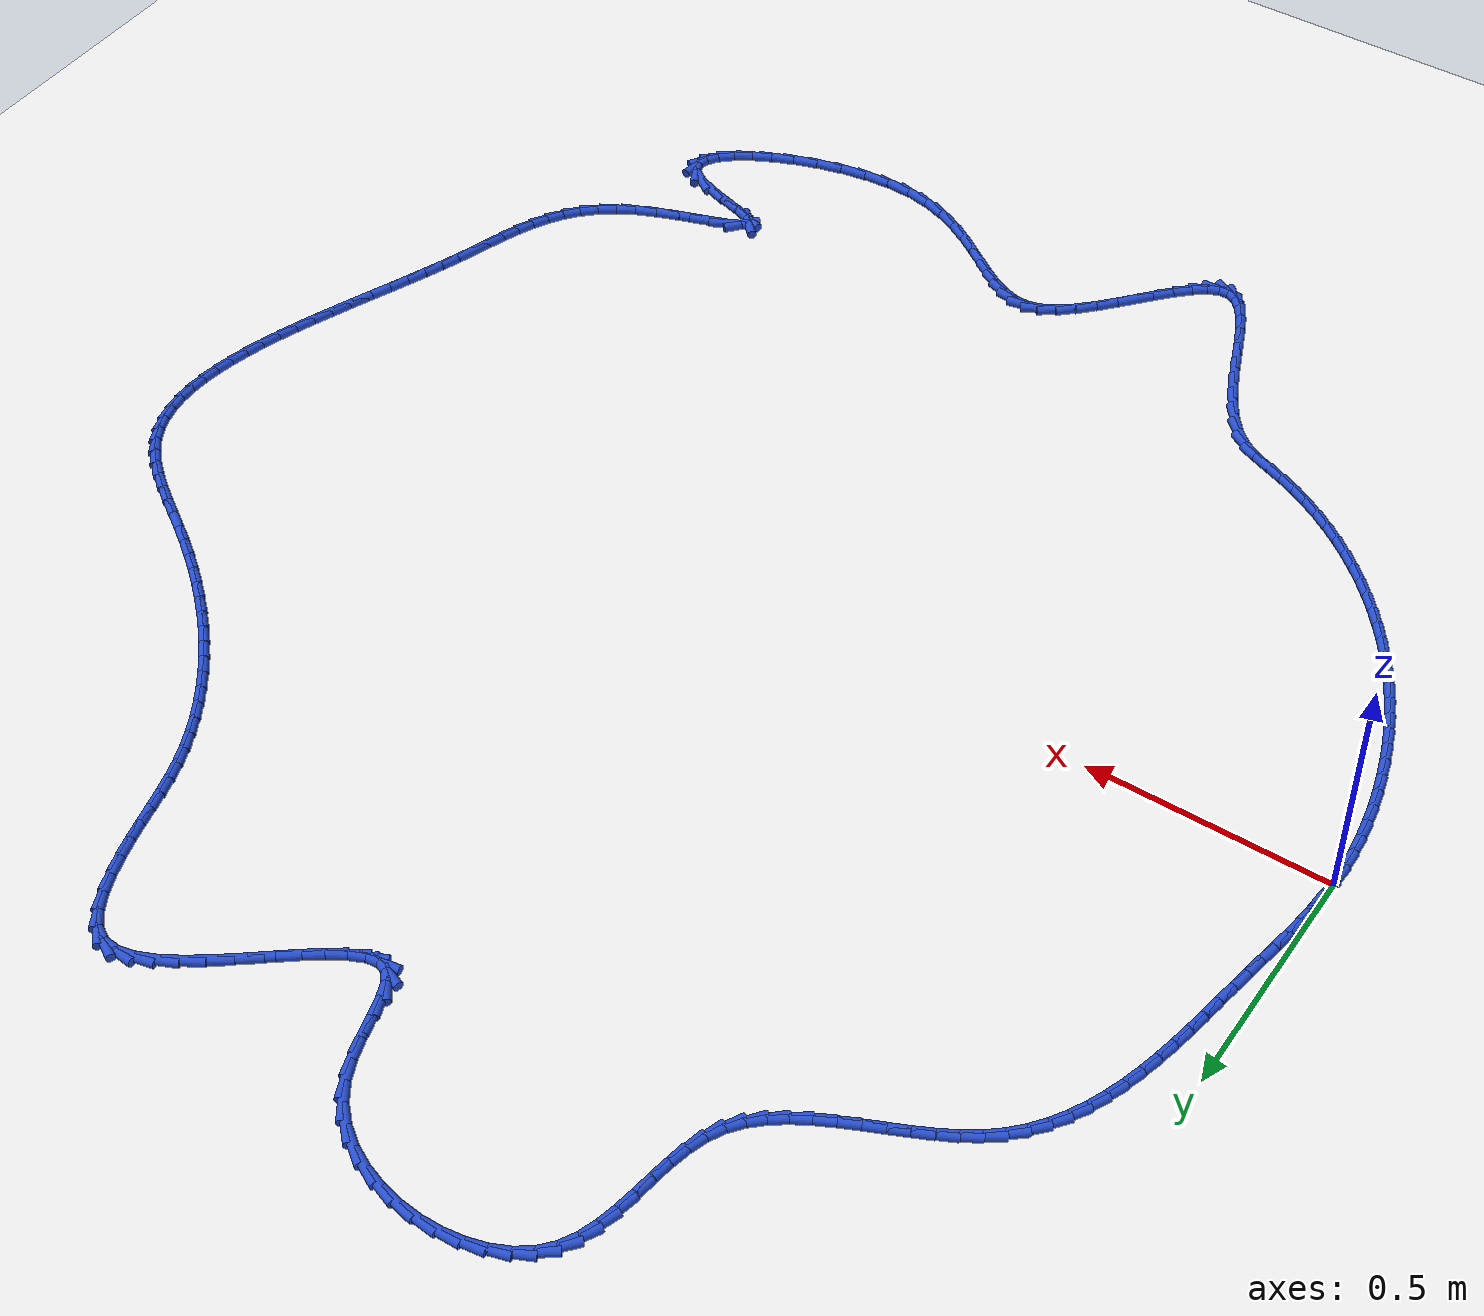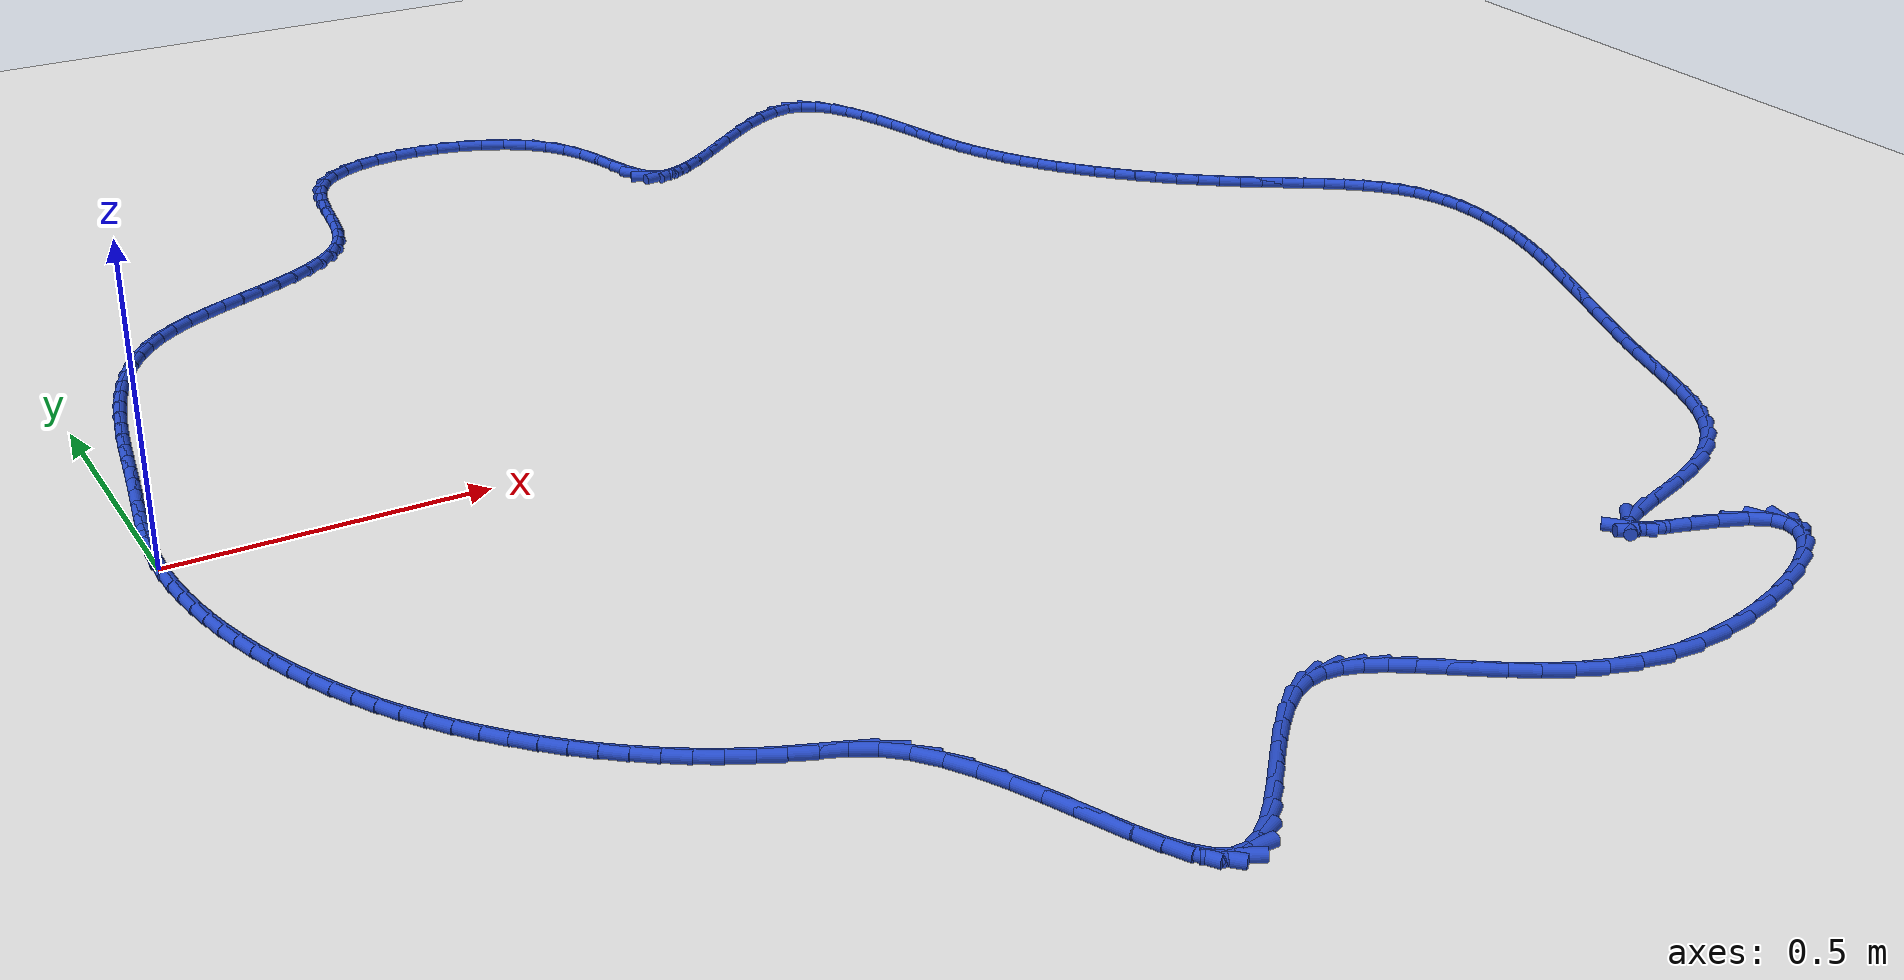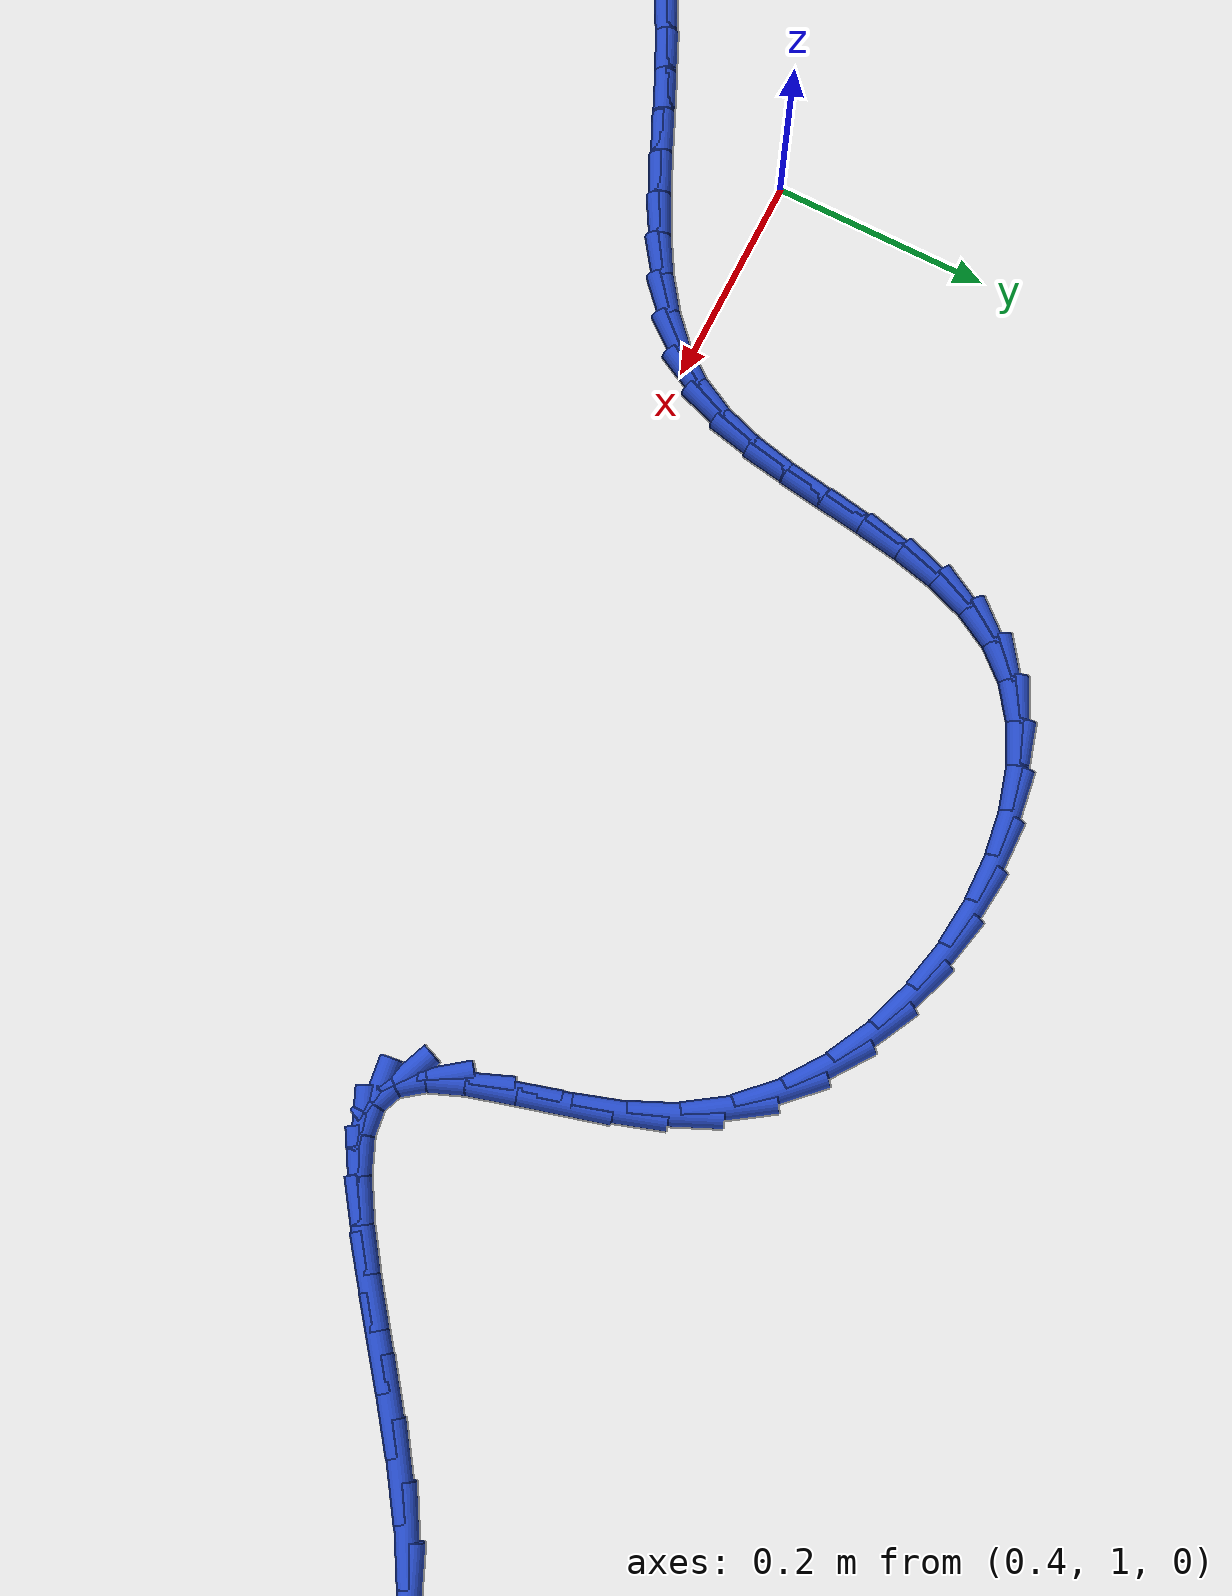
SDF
<sdf version="1.6">
 <world name="default">
  <light name="sun" type="directional">
   <pose>0 0 10 0 -0 0</pose>
   <diffuse>0.8 0.8 0.8 1</diffuse>
   <specular>0.2 0.2 0.2 1</specular>
   <attenuation>
    <range>1000</range>
    <constant>0.9</constant>
    <linear>0.01</linear>
    <quadratic>0.001</quadratic>
   </attenuation>
   <direction>-0.5 0.1 -0.9</direction>
  </light>
  <model name="ground_plane">
   <static>1</static>
   <link name="link">
    <collision name="collision">
     <geometry><plane><normal>0 0 1</normal><size>100 100</size></plane></geometry>
     <surface><friction><ode><mu>100</mu><mu2>50</mu2></ode></friction></surface>
    </collision>
    <visual name="visual">
     <cast_shadows>0</cast_shadows>
     <geometry><plane><normal>0 0 1</normal><size>100 100</size></plane></geometry>
     <material>
      <script><uri>file://media/materials/scripts/gazebo.material</uri><name>Gazebo/WhiteGlow</name></script>
     </material>
    </visual>
   </link>
  </model>
  <gravity>0 0 -9.8</gravity>
  <magnetic_field>6e-06 2.3e-05 -4.2e-05</magnetic_field>
  <atmosphere type="adiabatic"/>
  <physics name="default_physics" default="0" type="ode">
   <max_step_size>0.001</max_step_size>
   <real_time_factor>1</real_time_factor>
   <real_time_update_rate>1000</real_time_update_rate>
  </physics>
  <scene><ambient>0.4 0.4 0.4 1</ambient><background>0.7 0.7 0.7 1</background><shadows>1</shadows></scene>
  <spherical_coordinates>
   <surface_model>EARTH_WGS84</surface_model>
   <latitude_deg>0</latitude_deg>
   <longitude_deg>0</longitude_deg>
   <elevation>0</elevation>
   <heading_deg>0</heading_deg>
  </spherical_coordinates>
  <model name="line">
   <link name="link_0">
    <pose>9.540979117872439e-18 1.3183898417423734e-16 0.01 0 1.57 1.5213984638818068</pose>
    <collision name="collision">
     <geometry><cylinder><radius>0.01</radius><length>0.08</length></cylinder></geometry>
    </collision>
    <visual name="visual">
     <material>
      <script><name>Gazebo/Blue</name><uri>file://media/materials/scripts/gazebo.material</uri></script>
     </material>
     <geometry><cylinder><radius>0.01</radius><length>0.08</length></cylinder></geometry>
    </visual>
   </link>
   <link name="link_1">
    <pose>0.0018602137942777413 0.03762714361064959 0.01 0 1.57 1.4777009141318533</pose>
    <collision name="collision">
     <geometry><cylinder><radius>0.01</radius><length>0.08</length></cylinder></geometry>
    </collision>
    <visual name="visual">
     <material>
      <script><name>Gazebo/Blue</name><uri>file://media/materials/scripts/gazebo.material</uri></script>
     </material>
     <geometry><cylinder><radius>0.01</radius><length>0.08</length></cylinder></geometry>
    </visual>
   </link>
   <link name="link_2">
    <pose>0.005358032314779202 0.07509094192685227 0.01 0 1.57 1.4428675951724659</pose>
    <collision name="collision">
     <geometry><cylinder><radius>0.01</radius><length>0.08</length></cylinder></geometry>
    </collision>
    <visual name="visual">
     <material>
      <script><name>Gazebo/Blue</name><uri>file://media/materials/scripts/gazebo.material</uri></script>
     </material>
     <geometry><cylinder><radius>0.01</radius><length>0.08</length></cylinder></geometry>
    </visual>
   </link>
   <link name="link_3">
    <pose>0.010174533303189185 0.11253520469424017 0.01 0 1.57 1.417198399982593</pose>
    <collision name="collision">
     <geometry><cylinder><radius>0.01</radius><length>0.08</length></cylinder></geometry>
    </collision>
    <visual name="visual">
     <material>
      <script><name>Gazebo/Blue</name><uri>file://media/materials/scripts/gazebo.material</uri></script>
     </material>
     <geometry><cylinder><radius>0.01</radius><length>0.08</length></cylinder></geometry>
    </visual>
   </link>
   <link name="link_4">
    <pose>0.015990794501192476 0.15010374165844498 0.01 0 1.57 1.4007402308607189</pose>
    <collision name="collision">
     <geometry><cylinder><radius>0.01</radius><length>0.08</length></cylinder></geometry>
    </collision>
    <visual name="visual">
     <material>
      <script><name>Gazebo/Blue</name><uri>file://media/materials/scripts/gazebo.material</uri></script>
     </material>
     <geometry><cylinder><radius>0.01</radius><length>0.08</length></cylinder></geometry>
    </visual>
   </link>
   <link name="link_5">
    <pose>0.02248789365047388 0.1879403625650987 0.01 0 1.57 1.3933547497004122</pose>
    <collision name="collision">
     <geometry><cylinder><radius>0.01</radius><length>0.08</length></cylinder></geometry>
    </collision>
    <visual name="visual">
     <material>
      <script><name>Gazebo/Blue</name><uri>file://media/materials/scripts/gazebo.material</uri></script>
     </material>
     <geometry><cylinder><radius>0.01</radius><length>0.08</length></cylinder></geometry>
    </visual>
   </link>
   <link name="link_6">
    <pose>0.029346908492718177 0.22618887715983313 0.01 0 1.57 1.3947697535677857</pose>
    <collision name="collision">
     <geometry><cylinder><radius>0.01</radius><length>0.08</length></cylinder></geometry>
    </collision>
    <visual name="visual">
     <material>
      <script><name>Gazebo/Blue</name><uri>file://media/materials/scripts/gazebo.material</uri></script>
     </material>
     <geometry><cylinder><radius>0.01</radius><length>0.08</length></cylinder></geometry>
    </visual>
   </link>
   <link name="link_7">
    <pose>0.036248916769610166 0.26499309518828007 0.01 0 1.57 1.4028272110607247</pose>
    <collision name="collision">
     <geometry><cylinder><radius>0.01</radius><length>0.08</length></cylinder></geometry>
    </collision>
    <visual name="visual">
     <material>
      <script><name>Gazebo/Blue</name><uri>file://media/materials/scripts/gazebo.material</uri></script>
     </material>
     <geometry><cylinder><radius>0.01</radius><length>0.08</length></cylinder></geometry>
    </visual>
   </link>
   <link name="link_8">
    <pose>0.042939994531234114 0.30445292408419544 0.01 0 1.57 1.4070385849353564</pose>
    <collision name="collision">
     <geometry><cylinder><radius>0.01</radius><length>0.08</length></cylinder></geometry>
    </collision>
    <visual name="visual">
     <material>
      <script><name>Gazebo/Blue</name><uri>file://media/materials/scripts/gazebo.material</uri></script>
     </material>
     <geometry><cylinder><radius>0.01</radius><length>0.08</length></cylinder></geometry>
    </visual>
   </link>
   <link name="link_9">
    <pose>0.04954302084536876 0.3444137642948315 0.01 0 1.57 1.4039381576390337</pose>
    <collision name="collision">
     <geometry><cylinder><radius>0.01</radius><length>0.08</length></cylinder></geometry>
    </collision>
    <visual name="visual">
     <material>
      <script><name>Gazebo/Blue</name><uri>file://media/materials/scripts/gazebo.material</uri></script>
     </material>
     <geometry><cylinder><radius>0.01</radius><length>0.08</length></cylinder></geometry>
    </visual>
   </link>
   <link name="link_10">
    <pose>0.05631632638733266 0.38462952713695747 0.01 0 1.57 1.3936261280437061</pose>
    <collision name="collision">
     <geometry><cylinder><radius>0.01</radius><length>0.08</length></cylinder></geometry>
    </collision>
    <visual name="visual">
     <material>
      <script><name>Gazebo/Blue</name><uri>file://media/materials/scripts/gazebo.material</uri></script>
     </material>
     <geometry><cylinder><radius>0.01</radius><length>0.08</length></cylinder></geometry>
    </visual>
   </link>
   <link name="link_11">
    <pose>0.06351841929244793 0.4248540040641556 0.01 0 1.57 1.3759993044138343</pose>
    <collision name="collision">
     <geometry><cylinder><radius>0.01</radius><length>0.08</length></cylinder></geometry>
    </collision>
    <visual name="visual">
     <material>
      <script><name>Gazebo/Blue</name><uri>file://media/materials/scripts/gazebo.material</uri></script>
     </material>
     <geometry><cylinder><radius>0.01</radius><length>0.08</length></cylinder></geometry>
    </visual>
   </link>
   <link name="link_12">
    <pose>0.07140780769603669 0.4648409865300077 0.01 0 1.57 1.3507603679512552</pose>
    <collision name="collision">
     <geometry><cylinder><radius>0.01</radius><length>0.08</length></cylinder></geometry>
    </collision>
    <visual name="visual">
     <material>
      <script><name>Gazebo/Blue</name><uri>file://media/materials/scripts/gazebo.material</uri></script>
     </material>
     <geometry><cylinder><radius>0.01</radius><length>0.08</length></cylinder></geometry>
    </visual>
   </link>
   <link name="link_13">
    <pose>0.08024299973342101 0.504344265988096 0.01 0 1.57 1.3174328158271387</pose>
    <collision name="collision">
     <geometry><cylinder><radius>0.01</radius><length>0.08</length></cylinder></geometry>
    </collision>
    <visual name="visual">
     <material>
      <script><name>Gazebo/Blue</name><uri>file://media/materials/scripts/gazebo.material</uri></script>
     </material>
     <geometry><cylinder><radius>0.01</radius><length>0.08</length></cylinder></geometry>
    </visual>
   </link>
   <link name="link_14">
    <pose>0.09028250353992306 0.5431176338920027 0.01 0 1.57 1.2753842196467329</pose>
    <collision name="collision">
     <geometry><cylinder><radius>0.01</radius><length>0.08</length></cylinder></geometry>
    </collision>
    <visual name="visual">
     <material>
      <script><name>Gazebo/Blue</name><uri>file://media/materials/scripts/gazebo.material</uri></script>
     </material>
     <geometry><cylinder><radius>0.01</radius><length>0.08</length></cylinder></geometry>
    </visual>
   </link>
   <link name="link_15">
    <pose>0.10178482725086493 0.5809148816953095 0.01 0 1.57 1.2238695057610665</pose>
    <collision name="collision">
     <geometry><cylinder><radius>0.01</radius><length>0.08</length></cylinder></geometry>
    </collision>
    <visual name="visual">
     <material>
      <script><name>Gazebo/Blue</name><uri>file://media/materials/scripts/gazebo.material</uri></script>
     </material>
     <geometry><cylinder><radius>0.01</radius><length>0.08</length></cylinder></geometry>
    </visual>
   </link>
   <link name="link_16">
    <pose>0.11500847900156871 0.6174898008515988 0.01 0 1.57 1.1621110110754658</pose>
    <collision name="collision">
     <geometry><cylinder><radius>0.01</radius><length>0.08</length></cylinder></geometry>
    </collision>
    <visual name="visual">
     <material>
      <script><name>Gazebo/Blue</name><uri>file://media/materials/scripts/gazebo.material</uri></script>
     </material>
     <geometry><cylinder><radius>0.01</radius><length>0.08</length></cylinder></geometry>
    </visual>
   </link>
   <link name="link_17">
    <pose>0.13021196692735654 0.6525961828144523 0.01 0 1.57 1.0894358017726544</pose>
    <collision name="collision">
     <geometry><cylinder><radius>0.01</radius><length>0.08</length></cylinder></geometry>
    </collision>
    <visual name="visual">
     <material>
      <script><name>Gazebo/Blue</name><uri>file://media/materials/scripts/gazebo.material</uri></script>
     </material>
     <geometry><cylinder><radius>0.01</radius><length>0.08</length></cylinder></geometry>
    </visual>
   </link>
   <link name="link_18">
    <pose>0.1476537991635505 0.6859878190374523 0.01 0 1.57 1.0054873231868855</pose>
    <collision name="collision">
     <geometry><cylinder><radius>0.01</radius><length>0.08</length></cylinder></geometry>
    </collision>
    <visual name="visual">
     <material>
      <script><name>Gazebo/Blue</name><uri>file://media/materials/scripts/gazebo.material</uri></script>
     </material>
     <geometry><cylinder><radius>0.01</radius><length>0.08</length></cylinder></geometry>
    </visual>
   </link>
   <link name="link_19">
    <pose>0.16759248384547268 0.7174185009741809 0.01 0 1.57 0.9105074810997517</pose>
    <collision name="collision">
     <geometry><cylinder><radius>0.01</radius><length>0.08</length></cylinder></geometry>
    </collision>
    <visual name="visual">
     <material>
      <script><name>Gazebo/Blue</name><uri>file://media/materials/scripts/gazebo.material</uri></script>
     </material>
     <geometry><cylinder><radius>0.01</radius><length>0.08</length></cylinder></geometry>
    </visual>
   </link>
   <link name="link_20">
    <pose>0.1902865291084453 0.74664202007822 0.01 0 1.57 0.8056368817264867</pose>
    <collision name="collision">
     <geometry><cylinder><radius>0.01</radius><length>0.08</length></cylinder></geometry>
    </collision>
    <visual name="visual">
     <material>
      <script><name>Gazebo/Blue</name><uri>file://media/materials/scripts/gazebo.material</uri></script>
     </material>
     <geometry><cylinder><radius>0.01</radius><length>0.08</length></cylinder></geometry>
    </visual>
   </link>
   <link name="link_21">
    <pose>0.2159944430877903 0.7734121678031516 0.01 0 1.57 0.693253201119296</pose>
    <collision name="collision">
     <geometry><cylinder><radius>0.01</radius><length>0.08</length></cylinder></geometry>
    </collision>
    <visual name="visual">
     <material>
      <script><name>Gazebo/Blue</name><uri>file://media/materials/scripts/gazebo.material</uri></script>
     </material>
     <geometry><cylinder><radius>0.01</radius><length>0.08</length></cylinder></geometry>
    </visual>
   </link>
   <link name="link_22">
    <pose>0.24497061301210393 0.7974861511714872 0.01 0 1.57 0.5878919642807634</pose>
    <collision name="collision">
     <geometry><cylinder><radius>0.01</radius><length>0.08</length></cylinder></geometry>
    </collision>
    <visual name="visual">
     <material>
      <script><name>Gazebo/Blue</name><uri>file://media/materials/scripts/gazebo.material</uri></script>
     </material>
     <geometry><cylinder><radius>0.01</radius><length>0.08</length></cylinder></geometry>
    </visual>
   </link>
   <link name="link_23">
    <pose>0.2771178980864824 0.8189125374025596 0.01 0 1.57 0.5095602700968297</pose>
    <collision name="collision">
     <geometry><cylinder><radius>0.01</radius><length>0.08</length></cylinder></geometry>
    </collision>
    <visual name="visual">
     <material>
      <script><name>Gazebo/Blue</name><uri>file://media/materials/scripts/gazebo.material</uri></script>
     </material>
     <geometry><cylinder><radius>0.01</radius><length>0.08</length></cylinder></geometry>
    </visual>
   </link>
   <link name="link_24">
    <pose>0.3117239797503072 0.8382497771472255 0.01 0 1.57 0.45729567412060956</pose>
    <collision name="collision">
     <geometry><cylinder><radius>0.01</radius><length>0.08</length></cylinder></geometry>
    </collision>
    <visual name="visual">
     <material>
      <script><name>Gazebo/Blue</name><uri>file://media/materials/scripts/gazebo.material</uri></script>
     </material>
     <geometry><cylinder><radius>0.01</radius><length>0.08</length></cylinder></geometry>
    </visual>
   </link>
   <link name="link_25">
    <pose>0.3480144544973966 0.8561077794913734 0.01 0 1.57 0.4283943543734005</pose>
    <collision name="collision">
     <geometry><cylinder><radius>0.01</radius><length>0.08</length></cylinder></geometry>
    </collision>
    <visual name="visual">
     <material>
      <script><name>Gazebo/Blue</name><uri>file://media/materials/scripts/gazebo.material</uri></script>
     </material>
     <geometry><cylinder><radius>0.01</radius><length>0.08</length></cylinder></geometry>
    </visual>
   </link>
   <link name="link_26">
    <pose>0.38521491882156916 0.8730964535208919 0.01 0 1.57 0.42124980099251497</pose>
    <collision name="collision">
     <geometry><cylinder><radius>0.01</radius><length>0.08</length></cylinder></geometry>
    </collision>
    <visual name="visual">
     <material>
      <script><name>Gazebo/Blue</name><uri>file://media/materials/scripts/gazebo.material</uri></script>
     </material>
     <geometry><cylinder><radius>0.01</radius><length>0.08</length></cylinder></geometry>
    </visual>
   </link>
   <link name="link_27">
    <pose>0.42255096921664304 0.8898257083216696 0.01 0 1.57 0.43560560228455364</pose>
    <collision name="collision">
     <geometry><cylinder><radius>0.01</radius><length>0.08</length></cylinder></geometry>
    </collision>
    <visual name="visual">
     <material>
      <script><name>Gazebo/Blue</name><uri>file://media/materials/scripts/gazebo.material</uri></script>
     </material>
     <geometry><cylinder><radius>0.01</radius><length>0.08</length></cylinder></geometry>
    </visual>
   </link>
   <link name="link_28">
    <pose>0.4592482021764366 0.9069054529795945 0.01 0 1.57 0.47263384323847857</pose>
    <collision name="collision">
     <geometry><cylinder><radius>0.01</radius><length>0.08</length></cylinder></geometry>
    </collision>
    <visual name="visual">
     <material>
      <script><name>Gazebo/Blue</name><uri>file://media/materials/scripts/gazebo.material</uri></script>
     </material>
     <geometry><cylinder><radius>0.01</radius><length>0.08</length></cylinder></geometry>
    </visual>
   </link>
   <link name="link_29">
    <pose>0.494532214194768 0.9249455965805553 0.01 0 1.57 0.5349053730817138</pose>
    <collision name="collision">
     <geometry><cylinder><radius>0.01</radius><length>0.08</length></cylinder></geometry>
    </collision>
    <visual name="visual">
     <material>
      <script><name>Gazebo/Blue</name><uri>file://media/materials/scripts/gazebo.material</uri></script>
     </material>
     <geometry><cylinder><radius>0.01</radius><length>0.08</length></cylinder></geometry>
    </visual>
   </link>
   <link name="link_30">
    <pose>0.5276286017654558 0.94455604821044 0.01 0 1.57 0.6260728614755936</pose>
    <collision name="collision">
     <geometry><cylinder><radius>0.01</radius><length>0.08</length></cylinder></geometry>
    </collision>
    <visual name="visual">
     <material>
      <script><name>Gazebo/Blue</name><uri>file://media/materials/scripts/gazebo.material</uri></script>
     </material>
     <geometry><cylinder><radius>0.01</radius><length>0.08</length></cylinder></geometry>
    </visual>
   </link>
   <link name="link_31">
    <pose>0.5577629613823181 0.9663467169551375 0.01 0 1.57 0.749768314432401</pose>
    <collision name="collision">
     <geometry><cylinder><radius>0.01</radius><length>0.08</length></cylinder></geometry>
    </collision>
    <visual name="visual">
     <material>
      <script><name>Gazebo/Blue</name><uri>file://media/materials/scripts/gazebo.material</uri></script>
     </material>
     <geometry><cylinder><radius>0.01</radius><length>0.08</length></cylinder></geometry>
    </visual>
   </link>
   <link name="link_32">
    <pose>0.5841608895391733 0.9909275119005361 0.01 0 1.57 0.9069928572577938</pose>
    <collision name="collision">
     <geometry><cylinder><radius>0.01</radius><length>0.08</length></cylinder></geometry>
    </collision>
    <visual name="visual">
     <material>
      <script><name>Gazebo/Blue</name><uri>file://media/materials/scripts/gazebo.material</uri></script>
     </material>
     <geometry><cylinder><radius>0.01</radius><length>0.08</length></cylinder></geometry>
    </visual>
   </link>
   <link name="link_33">
    <pose>0.6060479827298397 1.018908342132524 0.01 0 1.57 1.0899137970166974</pose>
    <collision name="collision">
     <geometry><cylinder><radius>0.01</radius><length>0.08</length></cylinder></geometry>
    </collision>
    <visual name="visual">
     <material>
      <script><name>Gazebo/Blue</name><uri>file://media/materials/scripts/gazebo.material</uri></script>
     </material>
     <geometry><cylinder><radius>0.01</radius><length>0.08</length></cylinder></geometry>
    </visual>
   </link>
   <link name="link_34">
    <pose>0.6227133558785802 1.0508506773356325 0.01 0 1.57 1.249323673254769</pose>
    <collision name="collision">
     <geometry><cylinder><radius>0.01</radius><length>0.08</length></cylinder></geometry>
    </collision>
    <visual name="visual">
     <material>
      <script><name>Gazebo/Blue</name><uri>file://media/materials/scripts/gazebo.material</uri></script>
     </material>
     <geometry><cylinder><radius>0.01</radius><length>0.08</length></cylinder></geometry>
    </visual>
   </link>
   <link name="link_35">
    <pose>0.6345714150001026 1.086457835845379 0.01 0 1.57 1.3537976751370477</pose>
    <collision name="collision">
     <geometry><cylinder><radius>0.01</radius><length>0.08</length></cylinder></geometry>
    </collision>
    <visual name="visual">
     <material>
      <script><name>Gazebo/Blue</name><uri>file://media/materials/scripts/gazebo.material</uri></script>
     </material>
     <geometry><cylinder><radius>0.01</radius><length>0.08</length></cylinder></geometry>
    </visual>
   </link>
   <link name="link_36">
    <pose>0.6430019857467378 1.1246969032381031 0.01 0 1.57 1.4110650022134106</pose>
    <collision name="collision">
     <geometry><cylinder><radius>0.01</radius><length>0.08</length></cylinder></geometry>
    </collision>
    <visual name="visual">
     <material>
      <script><name>Gazebo/Blue</name><uri>file://media/materials/scripts/gazebo.material</uri></script>
     </material>
     <geometry><cylinder><radius>0.01</radius><length>0.08</length></cylinder></geometry>
    </visual>
   </link>
   <link name="link_37">
    <pose>0.6494162023737909 1.1645110890281178 0.01 0 1.57 1.4277523734582998</pose>
    <collision name="collision">
     <geometry><cylinder><radius>0.01</radius><length>0.08</length></cylinder></geometry>
    </collision>
    <visual name="visual">
     <material>
      <script><name>Gazebo/Blue</name><uri>file://media/materials/scripts/gazebo.material</uri></script>
     </material>
     <geometry><cylinder><radius>0.01</radius><length>0.08</length></cylinder></geometry>
    </visual>
   </link>
   <link name="link_38">
    <pose>0.6552251991365647 1.2048436027297342 0.01 0 1.57 1.4060738639525148</pose>
    <collision name="collision">
     <geometry><cylinder><radius>0.01</radius><length>0.08</length></cylinder></geometry>
    </collision>
    <visual name="visual">
     <material>
      <script><name>Gazebo/Blue</name><uri>file://media/materials/scripts/gazebo.material</uri></script>
     </material>
     <geometry><cylinder><radius>0.01</radius><length>0.08</length></cylinder></geometry>
    </visual>
   </link>
   <link name="link_39">
    <pose>0.6618401102903638 1.2446376538572648 0.01 0 1.57 1.3435786459064756</pose>
    <collision name="collision">
     <geometry><cylinder><radius>0.01</radius><length>0.08</length></cylinder></geometry>
    </collision>
    <visual name="visual">
     <material>
      <script><name>Gazebo/Blue</name><uri>file://media/materials/scripts/gazebo.material</uri></script>
     </material>
     <geometry><cylinder><radius>0.01</radius><length>0.08</length></cylinder></geometry>
    </visual>
   </link>
   <link name="link_40">
    <pose>0.6706720700904923 1.2828364519250215 0.01 0 1.57 1.2336509574036558</pose>
    <collision name="collision">
     <geometry><cylinder><radius>0.01</radius><length>0.08</length></cylinder></geometry>
    </collision>
    <visual name="visual">
     <material>
      <script><name>Gazebo/Blue</name><uri>file://media/materials/scripts/gazebo.material</uri></script>
     </material>
     <geometry><cylinder><radius>0.01</radius><length>0.08</length></cylinder></geometry>
    </visual>
   </link>
   <link name="link_41">
    <pose>0.6831322127922539 1.318383206447316 0.01 0 1.57 1.0682279757337139</pose>
    <collision name="collision">
     <geometry><cylinder><radius>0.01</radius><length>0.08</length></cylinder></geometry>
    </collision>
    <visual name="visual">
     <material>
      <script><name>Gazebo/Blue</name><uri>file://media/materials/scripts/gazebo.material</uri></script>
     </material>
     <geometry><cylinder><radius>0.01</radius><length>0.08</length></cylinder></geometry>
    </visual>
   </link>
   <link name="link_42">
    <pose>0.7006316726509526 1.35022112693846 0.01 0 1.57 0.8487314689223326</pose>
    <collision name="collision">
     <geometry><cylinder><radius>0.01</radius><length>0.08</length></cylinder></geometry>
    </collision>
    <visual name="visual">
     <material>
      <script><name>Gazebo/Blue</name><uri>file://media/materials/scripts/gazebo.material</uri></script>
     </material>
     <geometry><cylinder><radius>0.01</radius><length>0.08</length></cylinder></geometry>
    </visual>
   </link>
   <link name="link_43">
    <pose>0.7245030627952682 1.3773252909171676 0.01 0 1.57 0.626437201773708</pose>
    <collision name="collision">
     <geometry><cylinder><radius>0.01</radius><length>0.08</length></cylinder></geometry>
    </collision>
    <visual name="visual">
     <material>
      <script><name>Gazebo/Blue</name><uri>file://media/materials/scripts/gazebo.material</uri></script>
     </material>
     <geometry><cylinder><radius>0.01</radius><length>0.08</length></cylinder></geometry>
    </visual>
   </link>
   <link name="link_44">
    <pose>0.7547464578711351 1.3992115901270699 0.01 0 1.57 0.43820197652767523</pose>
    <collision name="collision">
     <geometry><cylinder><radius>0.01</radius><length>0.08</length></cylinder></geometry>
    </collision>
    <visual name="visual">
     <material>
      <script><name>Gazebo/Blue</name><uri>file://media/materials/scripts/gazebo.material</uri></script>
     </material>
     <geometry><cylinder><radius>0.01</radius><length>0.08</length></cylinder></geometry>
    </visual>
   </link>
   <link name="link_45">
    <pose>0.7902490270826533 1.4158475918931919 0.01 0 1.57 0.27943412489658653</pose>
    <collision name="collision">
     <geometry><cylinder><radius>0.01</radius><length>0.08</length></cylinder></geometry>
    </collision>
    <visual name="visual">
     <material>
      <script><name>Gazebo/Blue</name><uri>file://media/materials/scripts/gazebo.material</uri></script>
     </material>
     <geometry><cylinder><radius>0.01</radius><length>0.08</length></cylinder></geometry>
    </visual>
   </link>
   <link name="link_46">
    <pose>0.8298637923001349 1.4272147223252023 0.01 0 1.57 0.14182410572415036</pose>
    <collision name="collision">
     <geometry><cylinder><radius>0.01</radius><length>0.08</length></cylinder></geometry>
    </collision>
    <visual name="visual">
     <material>
      <script><name>Gazebo/Blue</name><uri>file://media/materials/scripts/gazebo.material</uri></script>
     </material>
     <geometry><cylinder><radius>0.01</radius><length>0.08</length></cylinder></geometry>
    </visual>
   </link>
   <link name="link_47">
    <pose>0.872443775393891 1.433294407532766 0.01 0 1.57 0.017423846027502545</pose>
    <collision name="collision">
     <geometry><cylinder><radius>0.01</radius><length>0.08</length></cylinder></geometry>
    </collision>
    <visual name="visual">
     <material>
      <script><name>Gazebo/Blue</name><uri>file://media/materials/scripts/gazebo.material</uri></script>
     </material>
     <geometry><cylinder><radius>0.01</radius><length>0.08</length></cylinder></geometry>
    </visual>
   </link>
   <link name="link_48">
    <pose>0.9168419982342343 1.434068073625551 0.01 0 1.57 -0.10063469008400559</pose>
    <collision name="collision">
     <geometry><cylinder><radius>0.01</radius><length>0.08</length></cylinder></geometry>
    </collision>
    <visual name="visual">
     <material>
      <script><name>Gazebo/Blue</name><uri>file://media/materials/scripts/gazebo.material</uri></script>
     </material>
     <geometry><cylinder><radius>0.01</radius><length>0.08</length></cylinder></geometry>
    </visual>
   </link>
   <link name="link_49">
    <pose>0.9619114826914754 1.4295171467132226 0.01 0 1.57 -0.21833486634404492</pose>
    <collision name="collision">
     <geometry><cylinder><radius>0.01</radius><length>0.08</length></cylinder></geometry>
    </collision>
    <visual name="visual">
     <material>
      <script><name>Gazebo/Blue</name><uri>file://media/materials/scripts/gazebo.material</uri></script>
     </material>
     <geometry><cylinder><radius>0.01</radius><length>0.08</length></cylinder></geometry>
    </visual>
   </link>
   <link name="link_50">
    <pose>1.0065052506359273 1.4196230529054479 0.01 0 1.57 -0.34114500668528774</pose>
    <collision name="collision">
     <geometry><cylinder><radius>0.01</radius><length>0.08</length></cylinder></geometry>
    </collision>
    <visual name="visual">
     <material>
      <script><name>Gazebo/Blue</name><uri>file://media/materials/scripts/gazebo.material</uri></script>
     </material>
     <geometry><cylinder><radius>0.01</radius><length>0.08</length></cylinder></geometry>
    </visual>
   </link>
   <link name="link_51">
    <pose>1.049476323937901 1.4043672183118932 0.01 0 1.57 -0.4742460753214095</pose>
    <collision name="collision">
     <geometry><cylinder><radius>0.01</radius><length>0.08</length></cylinder></geometry>
    </collision>
    <visual name="visual">
     <material>
      <script><name>Gazebo/Blue</name><uri>file://media/materials/scripts/gazebo.material</uri></script>
     </material>
     <geometry><cylinder><radius>0.01</radius><length>0.08</length></cylinder></geometry>
    </visual>
   </link>
   <link name="link_52">
    <pose>1.0896777244677087 1.3837310690422249 0.01 0 1.57 -0.6223879111697722</pose>
    <collision name="collision">
     <geometry><cylinder><radius>0.01</radius><length>0.08</length></cylinder></geometry>
    </collision>
    <visual name="visual">
     <material>
      <script><name>Gazebo/Blue</name><uri>file://media/materials/scripts/gazebo.material</uri></script>
     </material>
     <geometry><cylinder><radius>0.01</radius><length>0.08</length></cylinder></geometry>
    </visual>
   </link>
   <link name="link_53">
    <pose>1.1259624740956622 1.3576960312061104 0.01 0 1.57 -0.7890899661369595</pose>
    <collision name="collision">
     <geometry><cylinder><radius>0.01</radius><length>0.08</length></cylinder></geometry>
    </collision>
    <visual name="visual">
     <material>
      <script><name>Gazebo/Blue</name><uri>file://media/materials/scripts/gazebo.material</uri></script>
     </material>
     <geometry><cylinder><radius>0.01</radius><length>0.08</length></cylinder></geometry>
    </visual>
   </link>
   <link name="link_54">
    <pose>1.1571835946920728 1.3262435309132152 0.01 0 1.57 -0.9746696952326042</pose>
    <collision name="collision">
     <geometry><cylinder><radius>0.01</radius><length>0.08</length></cylinder></geometry>
    </collision>
    <visual name="visual">
     <material>
      <script><name>Gazebo/Blue</name><uri>file://media/materials/scripts/gazebo.material</uri></script>
     </material>
     <geometry><cylinder><radius>0.01</radius><length>0.08</length></cylinder></geometry>
    </visual>
   </link>
   <link name="link_55">
    <pose>1.1822045138408306 1.2893648424448048 0.01 0 1.57 -1.1458124868169501</pose>
    <collision name="collision">
     <geometry><cylinder><radius>0.01</radius><length>0.08</length></cylinder></geometry>
    </collision>
    <visual name="visual">
     <material>
      <script><name>Gazebo/Blue</name><uri>file://media/materials/scripts/gazebo.material</uri></script>
     </material>
     <geometry><cylinder><radius>0.01</radius><length>0.08</length></cylinder></geometry>
    </visual>
   </link>
   <link name="link_56">
    <pose>1.2009146612763038 1.2480222686581979 0.01 0 1.57 -1.252991450579234</pose>
    <collision name="collision">
     <geometry><cylinder><radius>0.01</radius><length>0.08</length></cylinder></geometry>
    </collision>
    <visual name="visual">
     <material>
      <script><name>Gazebo/Blue</name><uri>file://media/materials/scripts/gazebo.material</uri></script>
     </material>
     <geometry><cylinder><radius>0.01</radius><length>0.08</length></cylinder></geometry>
    </visual>
   </link>
   <link name="link_57">
    <pose>1.2150816394234953 1.2049556519144258 0.01 0 1.57 -1.3006480331451695</pose>
    <collision name="collision">
     <geometry><cylinder><radius>0.01</radius><length>0.08</length></cylinder></geometry>
    </collision>
    <visual name="visual">
     <material>
      <script><name>Gazebo/Blue</name><uri>file://media/materials/scripts/gazebo.material</uri></script>
     </material>
     <geometry><cylinder><radius>0.01</radius><length>0.08</length></cylinder></geometry>
    </visual>
   </link>
   <link name="link_58">
    <pose>1.2266736784243792 1.1630947125842663 0.01 0 1.57 -1.2874408476939674</pose>
    <collision name="collision">
     <geometry><cylinder><radius>0.01</radius><length>0.08</length></cylinder></geometry>
    </collision>
    <visual name="visual">
     <material>
      <script><name>Gazebo/Blue</name><uri>file://media/materials/scripts/gazebo.material</uri></script>
     </material>
     <geometry><cylinder><radius>0.01</radius><length>0.08</length></cylinder></geometry>
    </visual>
   </link>
   <link name="link_59">
    <pose>1.237659008420932 1.1253691710384963 0.01 0 1.57 -1.1879673774545032</pose>
    <collision name="collision">
     <geometry><cylinder><radius>0.01</radius><length>0.08</length></cylinder></geometry>
    </collision>
    <visual name="visual">
     <material>
      <script><name>Gazebo/Blue</name><uri>file://media/materials/scripts/gazebo.material</uri></script>
     </material>
     <geometry><cylinder><radius>0.01</radius><length>0.08</length></cylinder></geometry>
    </visual>
   </link>
   <link name="link_60">
    <pose>1.250005859555129 1.0947087476478963 0.01 0 1.57 -0.921823429640669</pose>
    <collision name="collision">
     <geometry><cylinder><radius>0.01</radius><length>0.08</length></cylinder></geometry>
    </collision>
    <visual name="visual">
     <material>
      <script><name>Gazebo/Blue</name><uri>file://media/materials/scripts/gazebo.material</uri></script>
     </material>
     <geometry><cylinder><radius>0.01</radius><length>0.08</length></cylinder></geometry>
    </visual>
   </link>
   <link name="link_61">
    <pose>1.2656824619689453 1.0740431627832419 0.01 0 1.57 -0.37753790260301073</pose>
    <collision name="collision">
     <geometry><cylinder><radius>0.01</radius><length>0.08</length></cylinder></geometry>
    </collision>
    <visual name="visual">
     <material>
      <script><name>Gazebo/Blue</name><uri>file://media/materials/scripts/gazebo.material</uri></script>
     </material>
     <geometry><cylinder><radius>0.01</radius><length>0.08</length></cylinder></geometry>
    </visual>
   </link>
   <link name="link_62">
    <pose>1.2863987260655592 1.0658279077658221 0.01 0 1.57 0.13519026092823513</pose>
    <collision name="collision">
     <geometry><cylinder><radius>0.01</radius><length>0.08</length></cylinder></geometry>
    </collision>
    <visual name="visual">
     <material>
      <script><name>Gazebo/Blue</name><uri>file://media/materials/scripts/gazebo.material</uri></script>
     </material>
     <geometry><cylinder><radius>0.01</radius><length>0.08</length></cylinder></geometry>
    </visual>
   </link>
   <link name="link_63">
    <pose>1.3121263214811052 1.069327373342965 0.01 0 1.57 0.4135358718772391</pose>
    <collision name="collision">
     <geometry><cylinder><radius>0.01</radius><length>0.08</length></cylinder></geometry>
    </collision>
    <visual name="visual">
     <material>
      <script><name>Gazebo/Blue</name><uri>file://media/materials/scripts/gazebo.material</uri></script>
     </material>
     <geometry><cylinder><radius>0.01</radius><length>0.08</length></cylinder></geometry>
    </visual>
   </link>
   <link name="link_64">
    <pose>1.3421200198013095 1.0824898530771336 0.01 0 1.57 0.55482379335384</pose>
    <collision name="collision">
     <geometry><cylinder><radius>0.01</radius><length>0.08</length></cylinder></geometry>
    </collision>
    <visual name="visual">
     <material>
      <script><name>Gazebo/Blue</name><uri>file://media/materials/scripts/gazebo.material</uri></script>
     </material>
     <geometry><cylinder><radius>0.01</radius><length>0.08</length></cylinder></geometry>
    </visual>
   </link>
   <link name="link_65">
    <pose>1.375632348659417 1.1032595210335434 0.01 0 1.57 0.6275881850826514</pose>
    <collision name="collision">
     <geometry><cylinder><radius>0.01</radius><length>0.08</length></cylinder></geometry>
    </collision>
    <visual name="visual">
     <material>
      <script><name>Gazebo/Blue</name><uri>file://media/materials/scripts/gazebo.material</uri></script>
     </material>
     <geometry><cylinder><radius>0.01</radius><length>0.08</length></cylinder></geometry>
    </visual>
   </link>
   <link name="link_66">
    <pose>1.4119158356886727 1.129580551277411 0.01 0 1.57 0.6614025121644797</pose>
    <collision name="collision">
     <geometry><cylinder><radius>0.01</radius><length>0.08</length></cylinder></geometry>
    </collision>
    <visual name="visual">
     <material>
      <script><name>Gazebo/Blue</name><uri>file://media/materials/scripts/gazebo.material</uri></script>
     </material>
     <geometry><cylinder><radius>0.01</radius><length>0.08</length></cylinder></geometry>
    </visual>
   </link>
   <link name="link_67">
    <pose>1.4502230085223218 1.1593971178739537 0.01 0 1.57 0.6683864508886445</pose>
    <collision name="collision">
     <geometry><cylinder><radius>0.01</radius><length>0.08</length></cylinder></geometry>
    </collision>
    <visual name="visual">
     <material>
      <script><name>Gazebo/Blue</name><uri>file://media/materials/scripts/gazebo.material</uri></script>
     </material>
     <geometry><cylinder><radius>0.01</radius><length>0.08</length></cylinder></geometry>
    </visual>
   </link>
   <link name="link_68">
    <pose>1.4898063947936084 1.1906533948883866 0.01 0 1.57 0.6523144195722065</pose>
    <collision name="collision">
     <geometry><cylinder><radius>0.01</radius><length>0.08</length></cylinder></geometry>
    </collision>
    <visual name="visual">
     <material>
      <script><name>Gazebo/Blue</name><uri>file://media/materials/scripts/gazebo.material</uri></script>
     </material>
     <geometry><cylinder><radius>0.01</radius><length>0.08</length></cylinder></geometry>
    </visual>
   </link>
   <link name="link_69">
    <pose>1.529918522135777 1.2212935563859262 0.01 0 1.57 0.6114463608501448</pose>
    <collision name="collision">
     <geometry><cylinder><radius>0.01</radius><length>0.08</length></cylinder></geometry>
    </collision>
    <visual name="visual">
     <material>
      <script><name>Gazebo/Blue</name><uri>file://media/materials/scripts/gazebo.material</uri></script>
     </material>
     <geometry><cylinder><radius>0.01</radius><length>0.08</length></cylinder></geometry>
    </visual>
   </link>
   <link name="link_70">
    <pose>1.5698119181820736 1.2492617764317895 0.01 0 1.57 0.5382280991515048</pose>
    <collision name="collision">
     <geometry><cylinder><radius>0.01</radius><length>0.08</length></cylinder></geometry>
    </collision>
    <visual name="visual">
     <material>
      <script><name>Gazebo/Blue</name><uri>file://media/materials/scripts/gazebo.material</uri></script>
     </material>
     <geometry><cylinder><radius>0.01</radius><length>0.08</length></cylinder></geometry>
    </visual>
   </link>
   <link name="link_71">
    <pose>1.6087391105657414 1.2725022290911916 0.01 0 1.57 0.4163719721982218</pose>
    <collision name="collision">
     <geometry><cylinder><radius>0.01</radius><length>0.08</length></cylinder></geometry>
    </collision>
    <visual name="visual">
     <material>
      <script><name>Gazebo/Blue</name><uri>file://media/materials/scripts/gazebo.material</uri></script>
     </material>
     <geometry><cylinder><radius>0.01</radius><length>0.08</length></cylinder></geometry>
    </visual>
   </link>
   <link name="link_72">
    <pose>1.6459526269200269 1.2889590884293498 0.01 0 1.57 0.21577944999510576</pose>
    <collision name="collision">
     <geometry><cylinder><radius>0.01</radius><length>0.08</length></cylinder></geometry>
    </collision>
    <visual name="visual">
     <material>
      <script><name>Gazebo/Blue</name><uri>file://media/materials/scripts/gazebo.material</uri></script>
     </material>
     <geometry><cylinder><radius>0.01</radius><length>0.08</length></cylinder></geometry>
    </visual>
   </link>
   <link name="link_73">
    <pose>1.680704994878173 1.2965765285114799 0.01 0 1.57 -0.10354138094093121</pose>
    <collision name="collision">
     <geometry><cylinder><radius>0.01</radius><length>0.08</length></cylinder></geometry>
    </collision>
    <visual name="visual">
     <material>
      <script><name>Gazebo/Blue</name><uri>file://media/materials/scripts/gazebo.material</uri></script>
     </material>
     <geometry><cylinder><radius>0.01</radius><length>0.08</length></cylinder></geometry>
    </visual>
   </link>
   <link name="link_74">
    <pose>1.7122487420734256 1.2932987234027982 0.01 0 1.57 -0.5223789625803251</pose>
    <collision name="collision">
     <geometry><cylinder><radius>0.01</radius><length>0.08</length></cylinder></geometry>
    </collision>
    <visual name="visual">
     <material>
      <script><name>Gazebo/Blue</name><uri>file://media/materials/scripts/gazebo.material</uri></script>
     </material>
     <geometry><cylinder><radius>0.01</radius><length>0.08</length></cylinder></geometry>
    </visual>
   </link>
   <link name="link_75">
    <pose>1.7398988280429615 1.2773798777785317 0.01 0 1.57 -0.8517555751140924</pose>
    <collision name="collision">
     <geometry><cylinder><radius>0.01</radius><length>0.08</length></cylinder></geometry>
    </collision>
    <visual name="visual">
     <material>
      <script><name>Gazebo/Blue</name><uri>file://media/materials/scripts/gazebo.material</uri></script>
     </material>
     <geometry><cylinder><radius>0.01</radius><length>0.08</length></cylinder></geometry>
    </visual>
   </link>
   <link name="link_76">
    <pose>1.763616810232701 1.2502851370581858 0.01 0 1.57 -1.047701369174803</pose>
    <collision name="collision">
     <geometry><cylinder><radius>0.01</radius><length>0.08</length></cylinder></geometry>
    </collision>
    <visual name="visual">
     <material>
      <script><name>Gazebo/Blue</name><uri>file://media/materials/scripts/gazebo.material</uri></script>
     </material>
     <geometry><cylinder><radius>0.01</radius><length>0.08</length></cylinder></geometry>
    </visual>
   </link>
   <link name="link_77">
    <pose>1.7837466504388926 1.215378628536477 0.01 0 1.57 -1.1651492482187171</pose>
    <collision name="collision">
     <geometry><cylinder><radius>0.01</radius><length>0.08</length></cylinder></geometry>
    </collision>
    <visual name="visual">
     <material>
      <script><name>Gazebo/Blue</name><uri>file://media/materials/scripts/gazebo.material</uri></script>
     </material>
     <geometry><cylinder><radius>0.01</radius><length>0.08</length></cylinder></geometry>
    </visual>
   </link>
   <link name="link_78">
    <pose>1.800637289773891 1.1760492062954426 0.01 0 1.57 -1.2369822908693664</pose>
    <collision name="collision">
     <geometry><cylinder><radius>0.01</radius><length>0.08</length></cylinder></geometry>
    </collision>
    <visual name="visual">
     <material>
      <script><name>Gazebo/Blue</name><uri>file://media/materials/scripts/gazebo.material</uri></script>
     </material>
     <geometry><cylinder><radius>0.01</radius><length>0.08</length></cylinder></geometry>
    </visual>
   </link>
   <link name="link_79">
    <pose>1.8146391057379005 1.135673946725689 0.01 0 1.57 -1.2830249694377305</pose>
    <collision name="collision">
     <geometry><cylinder><radius>0.01</radius><length>0.08</length></cylinder></geometry>
    </collision>
    <visual name="visual">
     <material>
      <script><name>Gazebo/Blue</name><uri>file://media/materials/scripts/gazebo.material</uri></script>
     </material>
     <geometry><cylinder><radius>0.01</radius><length>0.08</length></cylinder></geometry>
    </visual>
   </link>
   <link name="link_80">
    <pose>1.8262446132177588 1.09646446782016 0.01 0 1.57 -1.3141957135051476</pose>
    <collision name="collision">
     <geometry><cylinder><radius>0.01</radius><length>0.08</length></cylinder></geometry>
    </collision>
    <visual name="visual">
     <material>
      <script><name>Gazebo/Blue</name><uri>file://media/materials/scripts/gazebo.material</uri></script>
     </material>
     <geometry><cylinder><radius>0.01</radius><length>0.08</length></cylinder></geometry>
    </visual>
   </link>
   <link name="link_81">
    <pose>1.8362068017970958 1.0584966199884336 0.01 0 1.57 -1.3288820800078622</pose>
    <collision name="collision">
     <geometry><cylinder><radius>0.01</radius><length>0.08</length></cylinder></geometry>
    </collision>
    <visual name="visual">
     <material>
      <script><name>Gazebo/Blue</name><uri>file://media/materials/scripts/gazebo.material</uri></script>
     </material>
     <geometry><cylinder><radius>0.01</radius><length>0.08</length></cylinder></geometry>
    </visual>
   </link>
   <link name="link_82">
    <pose>1.8453065227550856 1.021617801099798 0.01 0 1.57 -1.3249666371870024</pose>
    <collision name="collision">
     <geometry><cylinder><radius>0.01</radius><length>0.08</length></cylinder></geometry>
    </collision>
    <visual name="visual">
     <material>
      <script><name>Gazebo/Blue</name><uri>file://media/materials/scripts/gazebo.material</uri></script>
     </material>
     <geometry><cylinder><radius>0.01</radius><length>0.08</length></cylinder></geometry>
    </visual>
   </link>
   <link name="link_83">
    <pose>1.854324627370905 0.9856754090235409 0.01 0 1.57 -1.3011419209189108</pose>
    <collision name="collision">
     <geometry><cylinder><radius>0.01</radius><length>0.08</length></cylinder></geometry>
    </collision>
    <visual name="visual">
     <material>
      <script><name>Gazebo/Blue</name><uri>file://media/materials/scripts/gazebo.material</uri></script>
     </material>
     <geometry><cylinder><radius>0.01</radius><length>0.08</length></cylinder></geometry>
    </visual>
   </link>
   <link name="link_84">
    <pose>1.864041966923729 0.9505168416289516 0.01 0 1.57 -1.2572409322914309</pose>
    <collision name="collision">
     <geometry><cylinder><radius>0.01</radius><length>0.08</length></cylinder></geometry>
    </collision>
    <visual name="visual">
     <material>
      <script><name>Gazebo/Blue</name><uri>file://media/materials/scripts/gazebo.material</uri></script>
     </material>
     <geometry><cylinder><radius>0.01</radius><length>0.08</length></cylinder></geometry>
    </visual>
   </link>
   <link name="link_85">
    <pose>1.8752374037061406 0.915989900417781 0.01 0 1.57 -1.2007810175958835</pose>
    <collision name="collision">
     <geometry><cylinder><radius>0.01</radius><length>0.08</length></cylinder></geometry>
    </collision>
    <visual name="visual">
     <material>
      <script><name>Gazebo/Blue</name><uri>file://media/materials/scripts/gazebo.material</uri></script>
     </material>
     <geometry><cylinder><radius>0.01</radius><length>0.08</length></cylinder></geometry>
    </visual>
   </link>
   <link name="link_86">
    <pose>1.8884227597774208 0.8819965783619493 0.01 0 1.57 -1.1454246966005144</pose>
    <collision name="collision">
     <geometry><cylinder><radius>0.01</radius><length>0.08</length></cylinder></geometry>
    </collision>
    <visual name="visual">
     <material>
      <script><name>Gazebo/Blue</name><uri>file://media/materials/scripts/gazebo.material</uri></script>
     </material>
     <geometry><cylinder><radius>0.01</radius><length>0.08</length></cylinder></geometry>
    </visual>
   </link>
   <link name="link_87">
    <pose>1.9035763982911384 0.8485471252380378 0.01 0 1.57 -1.0927626122115963</pose>
    <collision name="collision">
     <geometry><cylinder><radius>0.01</radius><length>0.08</length></cylinder></geometry>
    </collision>
    <visual name="visual">
     <material>
      <script><name>Gazebo/Blue</name><uri>file://media/materials/scripts/gazebo.material</uri></script>
     </material>
     <geometry><cylinder><radius>0.01</radius><length>0.08</length></cylinder></geometry>
    </visual>
   </link>
   <link name="link_88">
    <pose>1.9206132700866099 0.8156646593199829 0.01 0 1.57 -1.042771655752403</pose>
    <collision name="collision">
     <geometry><cylinder><radius>0.01</radius><length>0.08</length></cylinder></geometry>
    </collision>
    <visual name="visual">
     <material>
      <script><name>Gazebo/Blue</name><uri>file://media/materials/scripts/gazebo.material</uri></script>
     </material>
     <geometry><cylinder><radius>0.01</radius><length>0.08</length></cylinder></geometry>
    </visual>
   </link>
   <link name="link_89">
    <pose>1.9394483260031499 0.7833722988817231 0.01 0 1.57 -0.9953814151247429</pose>
    <collision name="collision">
     <geometry><cylinder><radius>0.01</radius><length>0.08</length></cylinder></geometry>
    </collision>
    <visual name="visual">
     <material>
      <script><name>Gazebo/Blue</name><uri>file://media/materials/scripts/gazebo.material</uri></script>
     </material>
     <geometry><cylinder><radius>0.01</radius><length>0.08</length></cylinder></geometry>
    </visual>
   </link>
   <link name="link_90">
    <pose>1.9599965168800741 0.7516931621971941 0.01 0 1.57 -0.9504860101871244</pose>
    <collision name="collision">
     <geometry><cylinder><radius>0.01</radius><length>0.08</length></cylinder></geometry>
    </collision>
    <visual name="visual">
     <material>
      <script><name>Gazebo/Blue</name><uri>file://media/materials/scripts/gazebo.material</uri></script>
     </material>
     <geometry><cylinder><radius>0.01</radius><length>0.08</length></cylinder></geometry>
    </visual>
   </link>
   <link name="link_91">
    <pose>1.982172793556698 0.7206503675403338 0.01 0 1.57 -0.9079545114887406</pose>
    <collision name="collision">
     <geometry><cylinder><radius>0.01</radius><length>0.08</length></cylinder></geometry>
    </collision>
    <visual name="visual">
     <material>
      <script><name>Gazebo/Blue</name><uri>file://media/materials/scripts/gazebo.material</uri></script>
     </material>
     <geometry><cylinder><radius>0.01</radius><length>0.08</length></cylinder></geometry>
    </visual>
   </link>
   <link name="link_92">
    <pose>2.005892106872338 0.6902670331850789 0.01 0 1.57 -0.8676396328762491</pose>
    <collision name="collision">
     <geometry><cylinder><radius>0.01</radius><length>0.08</length></cylinder></geometry>
    </collision>
    <visual name="visual">
     <material>
      <script><name>Gazebo/Blue</name><uri>file://media/materials/scripts/gazebo.material</uri></script>
     </material>
     <geometry><cylinder><radius>0.01</radius><length>0.08</length></cylinder></geometry>
    </visual>
   </link>
   <link name="link_93">
    <pose>2.0310694076663083 0.6605662774053669 0.01 0 1.57 -0.8293846563340639</pose>
    <collision name="collision">
     <geometry><cylinder><radius>0.01</radius><length>0.08</length></cylinder></geometry>
    </collision>
    <visual name="visual">
     <material>
      <script><name>Gazebo/Blue</name><uri>file://media/materials/scripts/gazebo.material</uri></script>
     </material>
     <geometry><cylinder><radius>0.01</radius><length>0.08</length></cylinder></geometry>
    </visual>
   </link>
   <link name="link_94">
    <pose>2.0576196467779253 0.6315712184751343 0.01 0 1.57 -0.7930287136258352</pose>
    <collision name="collision">
     <geometry><cylinder><radius>0.01</radius><length>0.08</length></cylinder></geometry>
    </collision>
    <visual name="visual">
     <material>
      <script><name>Gazebo/Blue</name><uri>file://media/materials/scripts/gazebo.material</uri></script>
     </material>
     <geometry><cylinder><radius>0.01</radius><length>0.08</length></cylinder></geometry>
    </visual>
   </link>
   <link name="link_95">
    <pose>2.0854577750465038 0.6033049746683188 0.01 0 1.57 -0.7584106347715007</pose>
    <collision name="collision">
     <geometry><cylinder><radius>0.01</radius><length>0.08</length></cylinder></geometry>
    </collision>
    <visual name="visual">
     <material>
      <script><name>Gazebo/Blue</name><uri>file://media/materials/scripts/gazebo.material</uri></script>
     </material>
     <geometry><cylinder><radius>0.01</radius><length>0.08</length></cylinder></geometry>
    </visual>
   </link>
   <link name="link_96">
    <pose>2.114498743311361 0.5757906642588572 0.01 0 1.57 -0.7253716023526059</pose>
    <collision name="collision">
     <geometry><cylinder><radius>0.01</radius><length>0.08</length></cylinder></geometry>
    </collision>
    <visual name="visual">
     <material>
      <script><name>Gazebo/Blue</name><uri>file://media/materials/scripts/gazebo.material</uri></script>
     </material>
     <geometry><cylinder><radius>0.01</radius><length>0.08</length></cylinder></geometry>
    </visual>
   </link>
   <link name="link_97">
    <pose>2.144657502411811 0.5490514055206867 0.01 0 1.57 -0.6937568444363156</pose>
    <collision name="collision">
     <geometry><cylinder><radius>0.01</radius><length>0.08</length></cylinder></geometry>
    </collision>
    <visual name="visual">
     <material>
      <script><name>Gazebo/Blue</name><uri>file://media/materials/scripts/gazebo.material</uri></script>
     </material>
     <geometry><cylinder><radius>0.01</radius><length>0.08</length></cylinder></geometry>
    </visual>
   </link>
   <link name="link_98">
    <pose>2.175849003187169 0.5231103167277441 0.01 0 1.57 -0.6634165737298975</pose>
    <collision name="collision">
     <geometry><cylinder><radius>0.01</radius><length>0.08</length></cylinder></geometry>
    </collision>
    <visual name="visual">
     <material>
      <script><name>Gazebo/Blue</name><uri>file://media/materials/scripts/gazebo.material</uri></script>
     </material>
     <geometry><cylinder><radius>0.01</radius><length>0.08</length></cylinder></geometry>
    </visual>
   </link>
   <link name="link_99">
    <pose>2.207988196476752 0.49799051615396644 0.01 0 1.57 -0.6342063473897935</pose>
    <collision name="collision">
     <geometry><cylinder><radius>0.01</radius><length>0.08</length></cylinder></geometry>
    </collision>
    <visual name="visual">
     <material>
      <script><name>Gazebo/Blue</name><uri>file://media/materials/scripts/gazebo.material</uri></script>
     </material>
     <geometry><cylinder><radius>0.01</radius><length>0.08</length></cylinder></geometry>
    </visual>
   </link>
   <link name="link_100">
    <pose>2.2409900331198744 0.4737151220732913 0.01 0 1.57 -0.6064828053947958</pose>
    <collision name="collision">
     <geometry><cylinder><radius>0.01</radius><length>0.08</length></cylinder></geometry>
    </collision>
    <visual name="visual">
     <material>
      <script><name>Gazebo/Blue</name><uri>file://media/materials/scripts/gazebo.material</uri></script>
     </material>
     <geometry><cylinder><radius>0.01</radius><length>0.08</length></cylinder></geometry>
    </visual>
   </link>
   <link name="link_101">
    <pose>2.274750701201509 0.4502954688941986 0.01 0 1.57 -0.5886555911151671</pose>
    <collision name="collision">
     <geometry><cylinder><radius>0.01</radius><length>0.08</length></cylinder></geometry>
    </collision>
    <visual name="visual">
     <material>
      <script><name>Gazebo/Blue</name><uri>file://media/materials/scripts/gazebo.material</uri></script>
     </material>
     <geometry><cylinder><radius>0.01</radius><length>0.08</length></cylinder></geometry>
    </visual>
   </link>
   <link name="link_102">
    <pose>2.308839381430467 0.4275375154788397 0.01 0 1.57 -0.5878506283056106</pose>
    <collision name="collision">
     <geometry><cylinder><radius>0.01</radius><length>0.08</length></cylinder></geometry>
    </collision>
    <visual name="visual">
     <material>
      <script><name>Gazebo/Blue</name><uri>file://media/materials/scripts/gazebo.material</uri></script>
     </material>
     <geometry><cylinder><radius>0.01</radius><length>0.08</length></cylinder></geometry>
    </visual>
   </link>
   <link name="link_103">
    <pose>2.3425475441071213 0.4050728058870897 0.01 0 1.57 -0.6049039102393619</pose>
    <collision name="collision">
     <geometry><cylinder><radius>0.01</radius><length>0.08</length></cylinder></geometry>
    </collision>
    <visual name="visual">
     <material>
      <script><name>Gazebo/Blue</name><uri>file://media/materials/scripts/gazebo.material</uri></script>
     </material>
     <geometry><cylinder><radius>0.01</radius><length>0.08</length></cylinder></geometry>
    </visual>
   </link>
   <link name="link_104">
    <pose>2.3751578387687227 0.38252734433729074 0.01 0 1.57 -0.641500957812803</pose>
    <collision name="collision">
     <geometry><cylinder><radius>0.01</radius><length>0.08</length></cylinder></geometry>
    </collision>
    <visual name="visual">
     <material>
      <script><name>Gazebo/Blue</name><uri>file://media/materials/scripts/gazebo.material</uri></script>
     </material>
     <geometry><cylinder><radius>0.01</radius><length>0.08</length></cylinder></geometry>
    </visual>
   </link>
   <link name="link_105">
    <pose>2.405952914952524 0.35952713504778383 0.01 0 1.57 -0.7004918208982428</pose>
    <collision name="collision">
     <geometry><cylinder><radius>0.01</radius><length>0.08</length></cylinder></geometry>
    </collision>
    <visual name="visual">
     <material>
      <script><name>Gazebo/Blue</name><uri>file://media/materials/scripts/gazebo.material</uri></script>
     </material>
     <geometry><cylinder><radius>0.01</radius><length>0.08</length></cylinder></geometry>
    </visual>
   </link>
   <link name="link_106">
    <pose>2.434215422195778 0.33569818223691134 0.01 0 1.57 -0.7857799107825099</pose>
    <collision name="collision">
     <geometry><cylinder><radius>0.01</radius><length>0.08</length></cylinder></geometry>
    </collision>
    <visual name="visual">
     <material>
      <script><name>Gazebo/Blue</name><uri>file://media/materials/scripts/gazebo.material</uri></script>
     </material>
     <geometry><cylinder><radius>0.01</radius><length>0.08</length></cylinder></geometry>
    </visual>
   </link>
   <link name="link_107">
    <pose>2.459228010035737 0.31066649012301445 0.01 0 1.57 -0.9014815843649162</pose>
    <collision name="collision">
     <geometry><cylinder><radius>0.01</radius><length>0.08</length></cylinder></geometry>
    </collision>
    <visual name="visual">
     <material>
      <script><name>Gazebo/Blue</name><uri>file://media/materials/scripts/gazebo.material</uri></script>
     </material>
     <geometry><cylinder><radius>0.01</radius><length>0.08</length></cylinder></geometry>
    </visual>
   </link>
   <link name="link_108">
    <pose>2.480277383181496 0.2840600881281208 0.01 0 1.57 -1.0386955093817873</pose>
    <collision name="collision">
     <geometry><cylinder><radius>0.01</radius><length>0.08</length></cylinder></geometry>
    </collision>
    <visual name="visual">
     <material>
      <script><name>Gazebo/Blue</name><uri>file://media/materials/scripts/gazebo.material</uri></script>
     </material>
     <geometry><cylinder><radius>0.01</radius><length>0.08</length></cylinder></geometry>
    </visual>
   </link>
   <link name="link_109">
    <pose>2.496988377695209 0.2556758727135417 0.01 0 1.57 -1.1744489095808566</pose>
    <collision name="collision">
     <geometry><cylinder><radius>0.01</radius><length>0.08</length></cylinder></geometry>
    </collision>
    <visual name="visual">
     <material>
      <script><name>Gazebo/Blue</name><uri>file://media/materials/scripts/gazebo.material</uri></script>
     </material>
     <geometry><cylinder><radius>0.01</radius><length>0.08</length></cylinder></geometry>
    </visual>
   </link>
   <link name="link_110">
    <pose>2.5095732434947133 0.22560410218871085 0.01 0 1.57 -1.3015843641063687</pose>
    <collision name="collision">
     <geometry><cylinder><radius>0.01</radius><length>0.08</length></cylinder></geometry>
    </collision>
    <visual name="visual">
     <material>
      <script><name>Gazebo/Blue</name><uri>file://media/materials/scripts/gazebo.material</uri></script>
     </material>
     <geometry><cylinder><radius>0.01</radius><length>0.08</length></cylinder></geometry>
    </visual>
   </link>
   <link name="link_111">
    <pose>2.5183029608211194 0.19396436552322818 0.01 0 1.57 -1.416521543204537</pose>
    <collision name="collision">
     <geometry><cylinder><radius>0.01</radius><length>0.08</length></cylinder></geometry>
    </collision>
    <visual name="visual">
     <material>
      <script><name>Gazebo/Blue</name><uri>file://media/materials/scripts/gazebo.material</uri></script>
     </material>
     <geometry><cylinder><radius>0.01</radius><length>0.08</length></cylinder></geometry>
    </visual>
   </link>
   <link name="link_112">
    <pose>2.5234485099155424 0.16087625168669223 0.01 0 1.57 -1.517606392508967</pose>
    <collision name="collision">
     <geometry><cylinder><radius>0.01</radius><length>0.08</length></cylinder></geometry>
    </collision>
    <visual name="visual">
     <material>
      <script><name>Gazebo/Blue</name><uri>file://media/materials/scripts/gazebo.material</uri></script>
     </material>
     <geometry><cylinder><radius>0.01</radius><length>0.08</length></cylinder></geometry>
    </visual>
   </link>
   <link name="link_113">
    <pose>2.5252808710190906 0.12645934964870295 0.01 0 1.57 1.5368498145802738</pose>
    <collision name="collision">
     <geometry><cylinder><radius>0.01</radius><length>0.08</length></cylinder></geometry>
    </collision>
    <visual name="visual">
     <material>
      <script><name>Gazebo/Blue</name><uri>file://media/materials/scripts/gazebo.material</uri></script>
     </material>
     <geometry><cylinder><radius>0.01</radius><length>0.08</length></cylinder></geometry>
    </visual>
   </link>
   <link name="link_114">
    <pose>2.524071024372879 0.09083324837885881 0.01 0 1.57 1.4627885748509004</pose>
    <collision name="collision">
     <geometry><cylinder><radius>0.01</radius><length>0.08</length></cylinder></geometry>
    </collision>
    <visual name="visual">
     <material>
      <script><name>Gazebo/Blue</name><uri>file://media/materials/scripts/gazebo.material</uri></script>
     </material>
     <geometry><cylinder><radius>0.01</radius><length>0.08</length></cylinder></geometry>
    </visual>
   </link>
   <link name="link_115">
    <pose>2.520089950218018 0.054117536846759864 0.01 0 1.57 1.4004790890435928</pose>
    <collision name="collision">
     <geometry><cylinder><radius>0.01</radius><length>0.08</length></cylinder></geometry>
    </collision>
    <visual name="visual">
     <material>
      <script><name>Gazebo/Blue</name><uri>file://media/materials/scripts/gazebo.material</uri></script>
     </material>
     <geometry><cylinder><radius>0.01</radius><length>0.08</length></cylinder></geometry>
    </visual>
   </link>
   <link name="link_116">
    <pose>2.5136086287956205 0.016431804022004958 0.01 0 1.57 1.3484953368697115</pose>
    <collision name="collision">
     <geometry><cylinder><radius>0.01</radius><length>0.08</length></cylinder></geometry>
    </collision>
    <visual name="visual">
     <material>
      <script><name>Gazebo/Blue</name><uri>file://media/materials/scripts/gazebo.material</uri></script>
     </material>
     <geometry><cylinder><radius>0.01</radius><length>0.08</length></cylinder></geometry>
    </visual>
   </link>
   <link name="link_117">
    <pose>2.504898040346798 -0.022104361125807614 0.01 0 1.57 1.3054999922596893</pose>
    <collision name="collision">
     <geometry><cylinder><radius>0.01</radius><length>0.08</length></cylinder></geometry>
    </collision>
    <visual name="visual">
     <material>
      <script><name>Gazebo/Blue</name><uri>file://media/materials/scripts/gazebo.material</uri></script>
     </material>
     <geometry><cylinder><radius>0.01</radius><length>0.08</length></cylinder></geometry>
    </visual>
   </link>
   <link name="link_118">
    <pose>2.4942291651126633 -0.061371369627076754 0.01 0 1.57 1.2703297530629334</pose>
    <collision name="collision">
     <geometry><cylinder><radius>0.01</radius><length>0.08</length></cylinder></geometry>
    </collision>
    <visual name="visual">
     <material>
      <script><name>Gazebo/Blue</name><uri>file://media/materials/scripts/gazebo.material</uri></script>
     </material>
     <geometry><cylinder><radius>0.01</radius><length>0.08</length></cylinder></geometry>
    </visual>
   </link>
   <link name="link_119">
    <pose>2.4818729833343287 -0.10124963251220417 0.01 0 1.57 1.2420205333198986</pose>
    <collision name="collision">
     <geometry><cylinder><radius>0.01</radius><length>0.08</length></cylinder></geometry>
    </collision>
    <visual name="visual">
     <material>
      <script><name>Gazebo/Blue</name><uri>file://media/materials/scripts/gazebo.material</uri></script>
     </material>
     <geometry><cylinder><radius>0.01</radius><length>0.08</length></cylinder></geometry>
    </visual>
   </link>
   <link name="link_120">
    <pose>2.468100475252906 -0.14161956081159058 0.01 0 1.57 1.2198033846943448</pose>
    <collision name="collision">
     <geometry><cylinder><radius>0.01</radius><length>0.08</length></cylinder></geometry>
    </collision>
    <visual name="visual">
     <material>
      <script><name>Gazebo/Blue</name><uri>file://media/materials/scripts/gazebo.material</uri></script>
     </material>
     <geometry><cylinder><radius>0.01</radius><length>0.08</length></cylinder></geometry>
    </visual>
   </link>
   <link name="link_121">
    <pose>2.4531826211095065 -0.1823615655556367 0.01 0 1.57 1.203089065928777</pose>
    <collision name="collision">
     <geometry><cylinder><radius>0.01</radius><length>0.08</length></cylinder></geometry>
    </collision>
    <visual name="visual">
     <material>
      <script><name>Gazebo/Blue</name><uri>file://media/materials/scripts/gazebo.material</uri></script>
     </material>
     <geometry><cylinder><radius>0.01</radius><length>0.08</length></cylinder></geometry>
    </visual>
   </link>
   <link name="link_122">
    <pose>2.437390401145244 -0.2233560577747445 0.01 0 1.57 1.1914506917664192</pose>
    <collision name="collision">
     <geometry><cylinder><radius>0.01</radius><length>0.08</length></cylinder></geometry>
    </collision>
    <visual name="visual">
     <material>
      <script><name>Gazebo/Blue</name><uri>file://media/materials/scripts/gazebo.material</uri></script>
     </material>
     <geometry><cylinder><radius>0.01</radius><length>0.08</length></cylinder></geometry>
    </visual>
   </link>
   <link name="link_123">
    <pose>2.420994795601228 -0.2644834484993125 0.01 0 1.57 1.1846090582874373</pose>
    <collision name="collision">
     <geometry><cylinder><radius>0.01</radius><length>0.08</length></cylinder></geometry>
    </collision>
    <visual name="visual">
     <material>
      <script><name>Gazebo/Blue</name><uri>file://media/materials/scripts/gazebo.material</uri></script>
     </material>
     <geometry><cylinder><radius>0.01</radius><length>0.08</length></cylinder></geometry>
    </visual>
   </link>
   <link name="link_124">
    <pose>2.4042667847185735 -0.30562414875974264 0.01 0 1.57 1.1824227588283078</pose>
    <collision name="collision">
     <geometry><cylinder><radius>0.01</radius><length>0.08</length></cylinder></geometry>
    </collision>
    <visual name="visual">
     <material>
      <script><name>Gazebo/Blue</name><uri>file://media/materials/scripts/gazebo.material</uri></script>
     </material>
     <geometry><cylinder><radius>0.01</radius><length>0.08</length></cylinder></geometry>
    </visual>
   </link>
   <link name="link_125">
    <pose>2.387477348738391 -0.3466585695864356 0.01 0 1.57 1.1848840761501118</pose>
    <collision name="collision">
     <geometry><cylinder><radius>0.01</radius><length>0.08</length></cylinder></geometry>
    </collision>
    <visual name="visual">
     <material>
      <script><name>Gazebo/Blue</name><uri>file://media/materials/scripts/gazebo.material</uri></script>
     </material>
     <geometry><cylinder><radius>0.01</radius><length>0.08</length></cylinder></geometry>
    </visual>
   </link>
   <link name="link_126">
    <pose>2.370897467901792 -0.38746712200979294 0.01 0 1.57 1.1921212350513166</pose>
    <collision name="collision">
     <geometry><cylinder><radius>0.01</radius><length>0.08</length></cylinder></geometry>
    </collision>
    <visual name="visual">
     <material>
      <script><name>Gazebo/Blue</name><uri>file://media/materials/scripts/gazebo.material</uri></script>
     </material>
     <geometry><cylinder><radius>0.01</radius><length>0.08</length></cylinder></geometry>
    </visual>
   </link>
   <link name="link_127">
    <pose>2.354798122449891 -0.42793021706021395 0.01 0 1.57 1.2044075522762234</pose>
    <collision name="collision">
     <geometry><cylinder><radius>0.01</radius><length>0.08</length></cylinder></geometry>
    </collision>
    <visual name="visual">
     <material>
      <script><name>Gazebo/Blue</name><uri>file://media/materials/scripts/gazebo.material</uri></script>
     </material>
     <geometry><cylinder><radius>0.01</radius><length>0.08</length></cylinder></geometry>
    </visual>
   </link>
   <link name="link_128">
    <pose>2.3394502926237983 -0.46792826576809987 0.01 0 1.57 1.2221780790470367</pose>
    <collision name="collision">
     <geometry><cylinder><radius>0.01</radius><length>0.08</length></cylinder></geometry>
    </collision>
    <visual name="visual">
     <material>
      <script><name>Gazebo/Blue</name><uri>file://media/materials/scripts/gazebo.material</uri></script>
     </material>
     <geometry><cylinder><radius>0.01</radius><length>0.08</length></cylinder></geometry>
    </visual>
   </link>
   <link name="link_129">
    <pose>2.3251249586646257 -0.5073416791638516 0.01 0 1.57 1.244852570734548</pose>
    <collision name="collision">
     <geometry><cylinder><radius>0.01</radius><length>0.08</length></cylinder></geometry>
    </collision>
    <visual name="visual">
     <material>
      <script><name>Gazebo/Blue</name><uri>file://media/materials/scripts/gazebo.material</uri></script>
     </material>
     <geometry><cylinder><radius>0.01</radius><length>0.08</length></cylinder></geometry>
    </visual>
   </link>
   <link name="link_130">
    <pose>2.3120420121365868 -0.5460487366459496 0.01 0 1.57 1.258116011314498</pose>
    <collision name="collision">
     <geometry><cylinder><radius>0.01</radius><length>0.08</length></cylinder></geometry>
    </collision>
    <visual name="visual">
     <material>
      <script><name>Gazebo/Blue</name><uri>file://media/materials/scripts/gazebo.material</uri></script>
     </material>
     <geometry><cylinder><radius>0.01</radius><length>0.08</length></cylinder></geometry>
    </visual>
   </link>
   <link name="link_131">
    <pose>2.299804609882451 -0.5839019848771962 0.01 0 1.57 1.2510163141170183</pose>
    <collision name="collision">
     <geometry><cylinder><radius>0.01</radius><length>0.08</length></cylinder></geometry>
    </collision>
    <visual name="visual">
     <material>
      <script><name>Gazebo/Blue</name><uri>file://media/materials/scripts/gazebo.material</uri></script>
     </material>
     <geometry><cylinder><radius>0.01</radius><length>0.08</length></cylinder></geometry>
    </visual>
   </link>
   <link name="link_132">
    <pose>2.287606900065139 -0.620736904978462 0.01 0 1.57 1.2218537954382922</pose>
    <collision name="collision">
     <geometry><cylinder><radius>0.01</radius><length>0.08</length></cylinder></geometry>
    </collision>
    <visual name="visual">
     <material>
      <script><name>Gazebo/Blue</name><uri>file://media/materials/scripts/gazebo.material</uri></script>
     </material>
     <geometry><cylinder><radius>0.01</radius><length>0.08</length></cylinder></geometry>
    </visual>
   </link>
   <link name="link_133">
    <pose>2.2746356967944745 -0.6563886720634444 0.01 0 1.57 1.169449940163644</pose>
    <collision name="collision">
     <geometry><cylinder><radius>0.01</radius><length>0.08</length></cylinder></geometry>
    </collision>
    <visual name="visual">
     <material>
      <script><name>Gazebo/Blue</name><uri>file://media/materials/scripts/gazebo.material</uri></script>
     </material>
     <geometry><cylinder><radius>0.01</radius><length>0.08</length></cylinder></geometry>
    </visual>
   </link>
   <link name="link_134">
    <pose>2.260077814180287 -0.6906924612458412 0.01 0 1.57 1.093525704193287</pose>
    <collision name="collision">
     <geometry><cylinder><radius>0.01</radius><length>0.08</length></cylinder></geometry>
    </collision>
    <visual name="visual">
     <material>
      <script><name>Gazebo/Blue</name><uri>file://media/materials/scripts/gazebo.material</uri></script>
     </material>
     <geometry><cylinder><radius>0.01</radius><length>0.08</length></cylinder></geometry>
    </visual>
   </link>
   <link name="link_135">
    <pose>2.243120066332404 -0.7234834476393496 0.01 0 1.57 0.9956169210976387</pose>
    <collision name="collision">
     <geometry><cylinder><radius>0.01</radius><length>0.08</length></cylinder></geometry>
    </collision>
    <visual name="visual">
     <material>
      <script><name>Gazebo/Blue</name><uri>file://media/materials/scripts/gazebo.material</uri></script>
     </material>
     <geometry><cylinder><radius>0.01</radius><length>0.08</length></cylinder></geometry>
    </visual>
   </link>
   <link name="link_136">
    <pose>2.222949267360653 -0.7545968063576652 0.01 0 1.57 0.8800103999019852</pose>
    <collision name="collision">
     <geometry><cylinder><radius>0.01</radius><length>0.08</length></cylinder></geometry>
    </collision>
    <visual name="visual">
     <material>
      <script><name>Gazebo/Blue</name><uri>file://media/materials/scripts/gazebo.material</uri></script>
     </material>
     <geometry><cylinder><radius>0.01</radius><length>0.08</length></cylinder></geometry>
    </visual>
   </link>
   <link name="link_137">
    <pose>2.1987522313748618 -0.7838677125144864 0.01 0 1.57 0.7539196230798381</pose>
    <collision name="collision">
     <geometry><cylinder><radius>0.01</radius><length>0.08</length></cylinder></geometry>
    </collision>
    <visual name="visual">
     <material>
      <script><name>Gazebo/Blue</name><uri>file://media/materials/scripts/gazebo.material</uri></script>
     </material>
     <geometry><cylinder><radius>0.01</radius><length>0.08</length></cylinder></geometry>
    </visual>
   </link>
   <link name="link_138">
    <pose>2.169715772484859 -0.8111313412235097 0.01 0 1.57 0.6262104765576222</pose>
    <collision name="collision">
     <geometry><cylinder><radius>0.01</radius><length>0.08</length></cylinder></geometry>
    </collision>
    <visual name="visual">
     <material>
      <script><name>Gazebo/Blue</name><uri>file://media/materials/scripts/gazebo.material</uri></script>
     </material>
     <geometry><cylinder><radius>0.01</radius><length>0.08</length></cylinder></geometry>
    </visual>
   </link>
   <link name="link_139">
    <pose>2.135026704800471 -0.8362228675984325 0.01 0 1.57 0.5050683813214808</pose>
    <collision name="collision">
     <geometry><cylinder><radius>0.01</radius><length>0.08</length></cylinder></geometry>
    </collision>
    <visual name="visual">
     <material>
      <script><name>Gazebo/Blue</name><uri>file://media/materials/scripts/gazebo.material</uri></script>
     </material>
     <geometry><cylinder><radius>0.01</radius><length>0.08</length></cylinder></geometry>
    </visual>
   </link>
   <link name="link_140">
    <pose>2.093871842431525 -0.8589774667529524 0.01 0 1.57 0.40317354967874675</pose>
    <collision name="collision">
     <geometry><cylinder><radius>0.01</radius><length>0.08</length></cylinder></geometry>
    </collision>
    <visual name="visual">
     <material>
      <script><name>Gazebo/Blue</name><uri>file://media/materials/scripts/gazebo.material</uri></script>
     </material>
     <geometry><cylinder><radius>0.01</radius><length>0.08</length></cylinder></geometry>
    </visual>
   </link>
   <link name="link_141">
    <pose>2.046233115714369 -0.8792972459943896 0.01 0 1.57 0.3458163592238009</pose>
    <collision name="collision">
     <geometry><cylinder><radius>0.01</radius><length>0.08</length></cylinder></geometry>
    </collision>
    <visual name="visual">
     <material>
      <script><name>Gazebo/Blue</name><uri>file://media/materials/scripts/gazebo.material</uri></script>
     </material>
     <geometry><cylinder><radius>0.01</radius><length>0.08</length></cylinder></geometry>
    </visual>
   </link>
   <link name="link_142">
    <pose>1.995961122814749 -0.8974099737291477 0.01 0 1.57 0.3268625783270204</pose>
    <collision name="collision">
     <geometry><cylinder><radius>0.01</radius><length>0.08</length></cylinder></geometry>
    </collision>
    <visual name="visual">
     <material>
      <script><name>Gazebo/Blue</name><uri>file://media/materials/scripts/gazebo.material</uri></script>
     </material>
     <geometry><cylinder><radius>0.01</radius><length>0.08</length></cylinder></geometry>
    </visual>
   </link>
   <link name="link_143">
    <pose>1.948081358380939 -0.9136423201294774 0.01 0 1.57 0.3480130493292259</pose>
    <collision name="collision">
     <geometry><cylinder><radius>0.01</radius><length>0.08</length></cylinder></geometry>
    </collision>
    <visual name="visual">
     <material>
      <script><name>Gazebo/Blue</name><uri>file://media/materials/scripts/gazebo.material</uri></script>
     </material>
     <geometry><cylinder><radius>0.01</radius><length>0.08</length></cylinder></geometry>
    </visual>
   </link>
   <link name="link_144">
    <pose>1.9076195859794642 -0.9283209780049353 0.01 0 1.57 0.44760740405013605</pose>
    <collision name="collision">
     <geometry><cylinder><radius>0.01</radius><length>0.08</length></cylinder></geometry>
    </collision>
    <visual name="visual">
     <material>
      <script><name>Gazebo/Blue</name><uri>file://media/materials/scripts/gazebo.material</uri></script>
     </material>
     <geometry><cylinder><radius>0.01</radius><length>0.08</length></cylinder></geometry>
    </visual>
   </link>
   <link name="link_145">
    <pose>1.8796015691768513 -0.9417726401650763 0.01 0 1.57 0.8718863694792514</pose>
    <collision name="collision">
     <geometry><cylinder><radius>0.01</radius><length>0.08</length></cylinder></geometry>
    </collision>
    <visual name="visual">
     <material>
      <script><name>Gazebo/Blue</name><uri>file://media/materials/scripts/gazebo.material</uri></script>
     </material>
     <geometry><cylinder><radius>0.01</radius><length>0.08</length></cylinder></geometry>
    </visual>
   </link>
   <link name="link_146">
    <pose>1.8690530715396236 -0.9543239994194561 0.01 0 1.57 -0.8100361347767994</pose>
    <collision name="collision">
     <geometry><cylinder><radius>0.01</radius><length>0.08</length></cylinder></geometry>
    </collision>
    <visual name="visual">
     <material>
      <script><name>Gazebo/Blue</name><uri>file://media/materials/scripts/gazebo.material</uri></script>
     </material>
     <geometry><cylinder><radius>0.01</radius><length>0.08</length></cylinder></geometry>
    </visual>
   </link>
   <link name="link_147">
    <pose>1.8804691249956074 -0.9663169192182226 0.01 0 1.57 -0.37304710965704696</pose>
    <collision name="collision">
     <geometry><cylinder><radius>0.01</radius><length>0.08</length></cylinder></geometry>
    </collision>
    <visual name="visual">
     <material>
      <script><name>Gazebo/Blue</name><uri>file://media/materials/scripts/gazebo.material</uri></script>
     </material>
     <geometry><cylinder><radius>0.01</radius><length>0.08</length></cylinder></geometry>
    </visual>
   </link>
   <link name="link_148">
    <pose>1.9110889003690217 -0.9783006673811888 0.01 0 1.57 -0.29434209963864494</pose>
    <collision name="collision">
     <geometry><cylinder><radius>0.01</radius><length>0.08</length></cylinder></geometry>
    </collision>
    <visual name="visual">
     <material>
      <script><name>Gazebo/Blue</name><uri>file://media/materials/scripts/gazebo.material</uri></script>
     </material>
     <geometry><cylinder><radius>0.01</radius><length>0.08</length></cylinder></geometry>
    </visual>
   </link>
   <link name="link_149">
    <pose>1.9528970394081127 -0.9909747092409539 0.01 0 1.57 -0.3038434600753206</pose>
    <collision name="collision">
     <geometry><cylinder><radius>0.01</radius><length>0.08</length></cylinder></geometry>
    </collision>
    <visual name="visual">
     <material>
      <script><name>Gazebo/Blue</name><uri>file://media/materials/scripts/gazebo.material</uri></script>
     </material>
     <geometry><cylinder><radius>0.01</radius><length>0.08</length></cylinder></geometry>
    </visual>
   </link>
   <link name="link_150">
    <pose>1.9977608323106262 -1.0050418645527033 0.01 0 1.57 -0.38587677177275365</pose>
    <collision name="collision">
     <geometry><cylinder><radius>0.01</radius><length>0.08</length></cylinder></geometry>
    </collision>
    <visual name="visual">
     <material>
      <script><name>Gazebo/Blue</name><uri>file://media/materials/scripts/gazebo.material</uri></script>
     </material>
     <geometry><cylinder><radius>0.01</radius><length>0.08</length></cylinder></geometry>
    </visual>
   </link>
   <link name="link_151">
    <pose>2.037547569274309 -1.021204953071622 0.01 0 1.57 -0.6150409497810844</pose>
    <collision name="collision">
     <geometry><cylinder><radius>0.01</radius><length>0.08</length></cylinder></geometry>
    </collision>
    <visual name="visual">
     <material>
      <script><name>Gazebo/Blue</name><uri>file://media/materials/scripts/gazebo.material</uri></script>
     </material>
     <geometry><cylinder><radius>0.01</radius><length>0.08</length></cylinder></geometry>
    </visual>
   </link>
   <link name="link_152">
    <pose>2.0643407982642725 -1.0401329987972223 0.01 0 1.57 -1.1120254504128737</pose>
    <collision name="collision">
     <geometry><cylinder><radius>0.01</radius><length>0.08</length></cylinder></geometry>
    </collision>
    <visual name="visual">
     <material>
      <script><name>Gazebo/Blue</name><uri>file://media/materials/scripts/gazebo.material</uri></script>
     </material>
     <geometry><cylinder><radius>0.01</radius><length>0.08</length></cylinder></geometry>
    </visual>
   </link>
   <link name="link_153">
    <pose>2.0750159523519907 -1.0617461722647676 0.01 0 1.57 1.4072876243334569</pose>
    <collision name="collision">
     <geometry><cylinder><radius>0.01</radius><length>0.08</length></cylinder></geometry>
    </collision>
    <visual name="visual">
     <material>
      <script><name>Gazebo/Blue</name><uri>file://media/materials/scripts/gazebo.material</uri></script>
     </material>
     <geometry><cylinder><radius>0.01</radius><length>0.08</length></cylinder></geometry>
    </visual>
   </link>
   <link name="link_154">
    <pose>2.0711413446693876 -1.0852312625922718 0.01 0 1.57 0.9738792158407034</pose>
    <collision name="collision">
     <geometry><cylinder><radius>0.01</radius><length>0.08</length></cylinder></geometry>
    </collision>
    <visual name="visual">
     <material>
      <script><name>Gazebo/Blue</name><uri>file://media/materials/scripts/gazebo.material</uri></script>
     </material>
     <geometry><cylinder><radius>0.01</radius><length>0.08</length></cylinder></geometry>
    </visual>
   </link>
   <link name="link_155">
    <pose>2.054481742401009 -1.109744357974294 0.01 0 1.57 0.7285139925244182</pose>
    <collision name="collision">
     <geometry><cylinder><radius>0.01</radius><length>0.08</length></cylinder></geometry>
    </collision>
    <visual name="visual">
     <material>
      <script><name>Gazebo/Blue</name><uri>file://media/materials/scripts/gazebo.material</uri></script>
     </material>
     <geometry><cylinder><radius>0.01</radius><length>0.08</length></cylinder></geometry>
    </visual>
   </link>
   <link name="link_156">
    <pose>2.026801912731399 -1.1344415466053925 0.01 0 1.57 0.5769351878763087</pose>
    <collision name="collision">
     <geometry><cylinder><radius>0.01</radius><length>0.08</length></cylinder></geometry>
    </collision>
    <visual name="visual">
     <material>
      <script><name>Gazebo/Blue</name><uri>file://media/materials/scripts/gazebo.material</uri></script>
     </material>
     <geometry><cylinder><radius>0.01</radius><length>0.08</length></cylinder></geometry>
    </visual>
   </link>
   <link name="link_157">
    <pose>1.9898666228451025 -1.158478916680125 0.01 0 1.57 0.46940499047257583</pose>
    <collision name="collision">
     <geometry><cylinder><radius>0.01</radius><length>0.08</length></cylinder></geometry>
    </collision>
    <visual name="visual">
     <material>
      <script><name>Gazebo/Blue</name><uri>file://media/materials/scripts/gazebo.material</uri></script>
     </material>
     <geometry><cylinder><radius>0.01</radius><length>0.08</length></cylinder></geometry>
    </visual>
   </link>
   <link name="link_158">
    <pose>1.9454406399266642 -1.181012556393049 0.01 0 1.57 0.38265718919222375</pose>
    <collision name="collision">
     <geometry><cylinder><radius>0.01</radius><length>0.08</length></cylinder></geometry>
    </collision>
    <visual name="visual">
     <material>
      <script><name>Gazebo/Blue</name><uri>file://media/materials/scripts/gazebo.material</uri></script>
     </material>
     <geometry><cylinder><radius>0.01</radius><length>0.08</length></cylinder></geometry>
    </visual>
   </link>
   <link name="link_159">
    <pose>1.8952887311606288 -1.2011985539387218 0.01 0 1.57 0.30430029285606114</pose>
    <collision name="collision">
     <geometry><cylinder><radius>0.01</radius><length>0.08</length></cylinder></geometry>
    </collision>
    <visual name="visual">
     <material>
      <script><name>Gazebo/Blue</name><uri>file://media/materials/scripts/gazebo.material</uri></script>
     </material>
     <geometry><cylinder><radius>0.01</radius><length>0.08</length></cylinder></geometry>
    </visual>
   </link>
   <link name="link_160">
    <pose>1.841175663731542 -1.218192997511703 0.01 0 1.57 0.22619998257850557</pose>
    <collision name="collision">
     <geometry><cylinder><radius>0.01</radius><length>0.08</length></cylinder></geometry>
    </collision>
    <visual name="visual">
     <material>
      <script><name>Gazebo/Blue</name><uri>file://media/materials/scripts/gazebo.material</uri></script>
     </material>
     <geometry><cylinder><radius>0.01</radius><length>0.08</length></cylinder></geometry>
    </visual>
   </link>
   <link name="link_161">
    <pose>1.7848662048239474 -1.231151975306549 0.01 0 1.57 0.14144332502048726</pose>
    <collision name="collision">
     <geometry><cylinder><radius>0.01</radius><length>0.08</length></cylinder></geometry>
    </collision>
    <visual name="visual">
     <material>
      <script><name>Gazebo/Blue</name><uri>file://media/materials/scripts/gazebo.material</uri></script>
     </material>
     <geometry><cylinder><radius>0.01</radius><length>0.08</length></cylinder></geometry>
    </visual>
   </link>
   <link name="link_162">
    <pose>1.7281251216223885 -1.2392315755178192 0.01 0 1.57 0.042500982297818304</pose>
    <collision name="collision">
     <geometry><cylinder><radius>0.01</radius><length>0.08</length></cylinder></geometry>
    </collision>
    <visual name="visual">
     <material>
      <script><name>Gazebo/Blue</name><uri>file://media/materials/scripts/gazebo.material</uri></script>
     </material>
     <geometry><cylinder><radius>0.01</radius><length>0.08</length></cylinder></geometry>
    </visual>
   </link>
   <link name="link_163">
    <pose>1.672717181311413 -1.2415878863400696 0.01 0 1.57 -0.08016382762010067</pose>
    <collision name="collision">
     <geometry><cylinder><radius>0.01</radius><length>0.08</length></cylinder></geometry>
    </collision>
    <visual name="visual">
     <material>
      <script><name>Gazebo/Blue</name><uri>file://media/materials/scripts/gazebo.material</uri></script>
     </material>
     <geometry><cylinder><radius>0.01</radius><length>0.08</length></cylinder></geometry>
    </visual>
   </link>
   <link name="link_164">
    <pose>1.6203994210405437 -1.2373848874058684 0.01 0 1.57 -0.2215063734440339</pose>
    <collision name="collision">
     <geometry><cylinder><radius>0.01</radius><length>0.08</length></cylinder></geometry>
    </collision>
    <visual name="visual">
     <material>
      <script><name>Gazebo/Blue</name><uri>file://media/materials/scripts/gazebo.material</uri></script>
     </material>
     <geometry><cylinder><radius>0.01</radius><length>0.08</length></cylinder></geometry>
    </visual>
   </link>
   <link name="link_165">
    <pose>1.5722002867480491 -1.2265303625300619 0.01 0 1.57 -0.35118830111972077</pose>
    <collision name="collision">
     <geometry><cylinder><radius>0.01</radius><length>0.08</length></cylinder></geometry>
    </collision>
    <visual name="visual">
     <material>
      <script><name>Gazebo/Blue</name><uri>file://media/materials/scripts/gazebo.material</uri></script>
     </material>
     <geometry><cylinder><radius>0.01</radius><length>0.08</length></cylinder></geometry>
    </visual>
   </link>
   <link name="link_166">
    <pose>1.527832650913773 -1.2102751381354144 0.01 0 1.57 -0.4594078575259606</pose>
    <collision name="collision">
     <geometry><cylinder><radius>0.01</radius><length>0.08</length></cylinder></geometry>
    </collision>
    <visual name="visual">
     <material>
      <script><name>Gazebo/Blue</name><uri>file://media/materials/scripts/gazebo.material</uri></script>
     </material>
     <geometry><cylinder><radius>0.01</radius><length>0.08</length></cylinder></geometry>
    </visual>
   </link>
   <link name="link_167">
    <pose>1.4868712489977087 -1.1900110619629676 0.01 0 1.57 -0.5422145541682972</pose>
    <collision name="collision">
     <geometry><cylinder><radius>0.01</radius><length>0.08</length></cylinder></geometry>
    </collision>
    <visual name="visual">
     <material>
      <script><name>Gazebo/Blue</name><uri>file://media/materials/scripts/gazebo.material</uri></script>
     </material>
     <geometry><cylinder><radius>0.01</radius><length>0.08</length></cylinder></geometry>
    </visual>
   </link>
   <link name="link_168">
    <pose>1.4488908164598455 -1.1671299817537615 0.01 0 1.57 -0.5975128736025582</pose>
    <collision name="collision">
     <geometry><cylinder><radius>0.01</radius><length>0.08</length></cylinder></geometry>
    </collision>
    <visual name="visual">
     <material>
      <script><name>Gazebo/Blue</name><uri>file://media/materials/scripts/gazebo.material</uri></script>
     </material>
     <geometry><cylinder><radius>0.01</radius><length>0.08</length></cylinder></geometry>
    </visual>
   </link>
   <link name="link_169">
    <pose>1.4134660887601742 -1.143023745248836 0.01 0 1.57 -0.6233830098594286</pose>
    <collision name="collision">
     <geometry><cylinder><radius>0.01</radius><length>0.08</length></cylinder></geometry>
    </collision>
    <visual name="visual">
     <material>
      <script><name>Gazebo/Blue</name><uri>file://media/materials/scripts/gazebo.material</uri></script>
     </material>
     <geometry><cylinder><radius>0.01</radius><length>0.08</length></cylinder></geometry>
    </visual>
   </link>
   <link name="link_170">
    <pose>1.3801718013586848 -1.1190842001892318 0.01 0 1.57 -0.6164104462927964</pose>
    <collision name="collision">
     <geometry><cylinder><radius>0.01</radius><length>0.08</length></cylinder></geometry>
    </collision>
    <visual name="visual">
     <material>
      <script><name>Gazebo/Blue</name><uri>file://media/materials/scripts/gazebo.material</uri></script>
     </material>
     <geometry><cylinder><radius>0.01</radius><length>0.08</length></cylinder></geometry>
    </visual>
   </link>
   <link name="link_171">
    <pose>1.34858268971537 -1.09670319431599 0.01 0 1.57 -0.570078913948525</pose>
    <collision name="collision">
     <geometry><cylinder><radius>0.01</radius><length>0.08</length></cylinder></geometry>
    </collision>
    <visual name="visual">
     <material>
      <script><name>Gazebo/Blue</name><uri>file://media/materials/scripts/gazebo.material</uri></script>
     </material>
     <geometry><cylinder><radius>0.01</radius><length>0.08</length></cylinder></geometry>
    </visual>
   </link>
   <link name="link_172">
    <pose>1.31827348929022 -1.0772725753701509 0.01 0 1.57 -0.47340728949423866</pose>
    <collision name="collision">
     <geometry><cylinder><radius>0.01</radius><length>0.08</length></cylinder></geometry>
    </collision>
    <visual name="visual">
     <material>
      <script><name>Gazebo/Blue</name><uri>file://media/materials/scripts/gazebo.material</uri></script>
     </material>
     <geometry><cylinder><radius>0.01</radius><length>0.08</length></cylinder></geometry>
    </visual>
   </link>
   <link name="link_173">
    <pose>1.288818935543225 -1.0621841910927543 0.01 0 1.57 -0.31177195960595694</pose>
    <collision name="collision">
     <geometry><cylinder><radius>0.01</radius><length>0.08</length></cylinder></geometry>
    </collision>
    <visual name="visual">
     <material>
      <script><name>Gazebo/Blue</name><uri>file://media/materials/scripts/gazebo.material</uri></script>
     </material>
     <geometry><cylinder><radius>0.01</radius><length>0.08</length></cylinder></geometry>
    </visual>
   </link>
   <link name="link_174">
    <pose>1.2597937639343761 -1.0528298892248413 0.01 0 1.57 -0.07663428547544678</pose>
    <collision name="collision">
     <geometry><cylinder><radius>0.01</radius><length>0.08</length></cylinder></geometry>
    </collision>
    <visual name="visual">
     <material>
      <script><name>Gazebo/Blue</name><uri>file://media/materials/scripts/gazebo.material</uri></script>
     </material>
     <geometry><cylinder><radius>0.01</radius><length>0.08</length></cylinder></geometry>
    </visual>
   </link>
   <link name="link_175">
    <pose>1.2307727099236634 -1.0506015175074521 0.01 0 1.57 0.21045556353992523</pose>
    <collision name="collision">
     <geometry><cylinder><radius>0.01</radius><length>0.08</length></cylinder></geometry>
    </collision>
    <visual name="visual">
     <material>
      <script><name>Gazebo/Blue</name><uri>file://media/materials/scripts/gazebo.material</uri></script>
     </material>
     <geometry><cylinder><radius>0.01</radius><length>0.08</length></cylinder></geometry>
    </visual>
   </link>
   <link name="link_176">
    <pose>1.2013305089710793 -1.0568909236816273 0.01 0 1.57 0.4791653981641039</pose>
    <collision name="collision">
     <geometry><cylinder><radius>0.01</radius><length>0.08</length></cylinder></geometry>
    </collision>
    <visual name="visual">
     <material>
      <script><name>Gazebo/Blue</name><uri>file://media/materials/scripts/gazebo.material</uri></script>
     </material>
     <geometry><cylinder><radius>0.01</radius><length>0.08</length></cylinder></geometry>
    </visual>
   </link>
   <link name="link_177">
    <pose>1.1711502791020694 -1.072571077078904 0.01 0 1.57 0.6550546164441563</pose>
    <collision name="collision">
     <geometry><cylinder><radius>0.01</radius><length>0.08</length></cylinder></geometry>
    </collision>
    <visual name="visual">
     <material>
      <script><name>Gazebo/Blue</name><uri>file://media/materials/scripts/gazebo.material</uri></script>
     </material>
     <geometry><cylinder><radius>0.01</radius><length>0.08</length></cylinder></geometry>
    </visual>
   </link>
   <link name="link_178">
    <pose>1.140399976888232 -1.0961937964598278 0.01 0 1.57 0.7598009761798901</pose>
    <collision name="collision">
     <geometry><cylinder><radius>0.01</radius><length>0.08</length></cylinder></geometry>
    </collision>
    <visual name="visual">
     <material>
      <script><name>Gazebo/Blue</name><uri>file://media/materials/scripts/gazebo.material</uri></script>
     </material>
     <geometry><cylinder><radius>0.01</radius><length>0.08</length></cylinder></geometry>
    </visual>
   </link>
   <link name="link_179">
    <pose>1.1093830782325493 -1.1256621056903924 0.01 0 1.57 0.8202281186090637</pose>
    <collision name="collision">
     <geometry><cylinder><radius>0.01</radius><length>0.08</length></cylinder></geometry>
    </collision>
    <visual name="visual">
     <material>
      <script><name>Gazebo/Blue</name><uri>file://media/materials/scripts/gazebo.material</uri></script>
     </material>
     <geometry><cylinder><radius>0.01</radius><length>0.08</length></cylinder></geometry>
    </visual>
   </link>
   <link name="link_180">
    <pose>1.0784030653181953 -1.158878998570368 0.01 0 1.57 0.849862936586433</pose>
    <collision name="collision">
     <geometry><cylinder><radius>0.01</radius><length>0.08</length></cylinder></geometry>
    </collision>
    <visual name="visual">
     <material>
      <script><name>Gazebo/Blue</name><uri>file://media/materials/scripts/gazebo.material</uri></script>
     </material>
     <geometry><cylinder><radius>0.01</radius><length>0.08</length></cylinder></geometry>
    </visual>
   </link>
   <link name="link_181">
    <pose>1.0477634203283401 -1.1937474688995269 0.01 0 1.57 0.8540162304549302</pose>
    <collision name="collision">
     <geometry><cylinder><radius>0.01</radius><length>0.08</length></cylinder></geometry>
    </collision>
    <visual name="visual">
     <material>
      <script><name>Gazebo/Blue</name><uri>file://media/materials/scripts/gazebo.material</uri></script>
     </material>
     <geometry><cylinder><radius>0.01</radius><length>0.08</length></cylinder></geometry>
    </visual>
   </link>
   <link name="link_182">
    <pose>1.0177676254461565 -1.22817051047764 0.01 0 1.57 0.8318473701227223</pose>
    <collision name="collision">
     <geometry><cylinder><radius>0.01</radius><length>0.08</length></cylinder></geometry>
    </collision>
    <visual name="visual">
     <material>
      <script><name>Gazebo/Blue</name><uri>file://media/materials/scripts/gazebo.material</uri></script>
     </material>
     <geometry><cylinder><radius>0.01</radius><length>0.08</length></cylinder></geometry>
    </visual>
   </link>
   <link name="link_183">
    <pose>0.988719162854816 -1.2600511171044788 0.01 0 1.57 0.7752877768477786</pose>
    <collision name="collision">
     <geometry><cylinder><radius>0.01</radius><length>0.08</length></cylinder></geometry>
    </collision>
    <visual name="visual">
     <material>
      <script><name>Gazebo/Blue</name><uri>file://media/materials/scripts/gazebo.material</uri></script>
     </material>
     <geometry><cylinder><radius>0.01</radius><length>0.08</length></cylinder></geometry>
    </visual>
   </link>
   <link name="link_184">
    <pose>0.9609215147374897 -1.2872922825798159 0.01 0 1.57 0.6632526771141637</pose>
    <collision name="collision">
     <geometry><cylinder><radius>0.01</radius><length>0.08</length></cylinder></geometry>
    </collision>
    <visual name="visual">
     <material>
      <script><name>Gazebo/Blue</name><uri>file://media/materials/scripts/gazebo.material</uri></script>
     </material>
     <geometry><cylinder><radius>0.01</radius><length>0.08</length></cylinder></geometry>
    </visual>
   </link>
   <link name="link_185">
    <pose>0.9346781632773509 -1.3077970007034205 0.01 0 1.57 0.44639250683647097</pose>
    <collision name="collision">
     <geometry><cylinder><radius>0.01</radius><length>0.08</length></cylinder></geometry>
    </collision>
    <visual name="visual">
     <material>
      <script><name>Gazebo/Blue</name><uri>file://media/materials/scripts/gazebo.material</uri></script>
     </material>
     <geometry><cylinder><radius>0.01</radius><length>0.08</length></cylinder></geometry>
    </visual>
   </link>
   <link name="link_186">
    <pose>0.9102925906575712 -1.3194682652750653 0.01 0 1.57 0.03622957111138822</pose>
    <collision name="collision">
     <geometry><cylinder><radius>0.01</radius><length>0.08</length></cylinder></geometry>
    </collision>
    <visual name="visual">
     <material>
      <script><name>Gazebo/Blue</name><uri>file://media/materials/scripts/gazebo.material</uri></script>
     </material>
     <geometry><cylinder><radius>0.01</radius><length>0.08</length></cylinder></geometry>
    </visual>
   </link>
   <link name="link_187">
    <pose>0.8880543527877633 -1.3202742997883088 0.01 0 1.57 -0.47499812535406755</pose>
    <collision name="collision">
     <geometry><cylinder><radius>0.01</radius><length>0.08</length></cylinder></geometry>
    </collision>
    <visual name="visual">
     <material>
      <script><name>Gazebo/Blue</name><uri>file://media/materials/scripts/gazebo.material</uri></script>
     </material>
     <geometry><cylinder><radius>0.01</radius><length>0.08</length></cylinder></geometry>
    </visual>
   </link>
   <link name="link_188">
    <pose>0.8678860057845245 -1.3099023291636365 0.01 0 1.57 -0.8227487343417692</pose>
    <collision name="collision">
     <geometry><cylinder><radius>0.01</radius><length>0.08</length></cylinder></geometry>
    </collision>
    <visual name="visual">
     <material>
      <script><name>Gazebo/Blue</name><uri>file://media/materials/scripts/gazebo.material</uri></script>
     </material>
     <geometry><cylinder><radius>0.01</radius><length>0.08</length></cylinder></geometry>
    </visual>
   </link>
   <link name="link_189">
    <pose>0.8493151216021689 -1.2898896565817948 0.01 0 1.57 -1.0134805519124364</pose>
    <collision name="collision">
     <geometry><cylinder><radius>0.01</radius><length>0.08</length></cylinder></geometry>
    </collision>
    <visual name="visual">
     <material>
      <script><name>Gazebo/Blue</name><uri>file://media/materials/scripts/gazebo.material</uri></script>
     </material>
     <geometry><cylinder><radius>0.01</radius><length>0.08</length></cylinder></geometry>
    </visual>
   </link>
   <link name="link_190">
    <pose>0.8318497395716151 -1.261865074668822 0.01 0 1.57 -1.1153665813827056</pose>
    <collision name="collision">
     <geometry><cylinder><radius>0.01</radius><length>0.08</length></cylinder></geometry>
    </collision>
    <visual name="visual">
     <material>
      <script><name>Gazebo/Blue</name><uri>file://media/materials/scripts/gazebo.material</uri></script>
     </material>
     <geometry><cylinder><radius>0.01</radius><length>0.08</length></cylinder></geometry>
    </visual>
   </link>
   <link name="link_191">
    <pose>0.8149978990237823 -1.2274573760507583 0.01 0 1.57 -1.1670584751658954</pose>
    <collision name="collision">
     <geometry><cylinder><radius>0.01</radius><length>0.08</length></cylinder></geometry>
    </collision>
    <visual name="visual">
     <material>
      <script><name>Gazebo/Blue</name><uri>file://media/materials/scripts/gazebo.material</uri></script>
     </material>
     <geometry><cylinder><radius>0.01</radius><length>0.08</length></cylinder></geometry>
    </visual>
   </link>
   <link name="link_192">
    <pose>0.7982676392895888 -1.188295353353641 0.01 0 1.57 -1.1865117017534481</pose>
    <collision name="collision">
     <geometry><cylinder><radius>0.01</radius><length>0.08</length></cylinder></geometry>
    </collision>
    <visual name="visual">
     <material>
      <script><name>Gazebo/Blue</name><uri>file://media/materials/scripts/gazebo.material</uri></script>
     </material>
     <geometry><cylinder><radius>0.01</radius><length>0.08</length></cylinder></geometry>
    </visual>
   </link>
   <link name="link_193">
    <pose>0.7811669996999551 -1.146007799203513 0.01 0 1.57 -1.1814758270986385</pose>
    <collision name="collision">
     <geometry><cylinder><radius>0.01</radius><length>0.08</length></cylinder></geometry>
    </collision>
    <visual name="visual">
     <material>
      <script><name>Gazebo/Blue</name><uri>file://media/materials/scripts/gazebo.material</uri></script>
     </material>
     <geometry><cylinder><radius>0.01</radius><length>0.08</length></cylinder></geometry>
    </visual>
   </link>
   <link name="link_194">
    <pose>0.7632040195857996 -1.1022235062264114 0.01 0 1.57 -1.154174552740944</pose>
    <collision name="collision">
     <geometry><cylinder><radius>0.01</radius><length>0.08</length></cylinder></geometry>
    </collision>
    <visual name="visual">
     <material>
      <script><name>Gazebo/Blue</name><uri>file://media/materials/scripts/gazebo.material</uri></script>
     </material>
     <geometry><cylinder><radius>0.01</radius><length>0.08</length></cylinder></geometry>
    </visual>
   </link>
   <link name="link_195">
    <pose>0.7438867382780415 -1.0585712670483758 0.01 0 1.57 -1.1029971567979153</pose>
    <collision name="collision">
     <geometry><cylinder><radius>0.01</radius><length>0.08</length></cylinder></geometry>
    </collision>
    <visual name="visual">
     <material>
      <script><name>Gazebo/Blue</name><uri>file://media/materials/scripts/gazebo.material</uri></script>
     </material>
     <geometry><cylinder><radius>0.01</radius><length>0.08</length></cylinder></geometry>
    </visual>
   </link>
   <link name="link_196">
    <pose>0.7227231951075996 -1.0166798742954455 0.01 0 1.57 -1.022759254259136</pose>
    <collision name="collision">
     <geometry><cylinder><radius>0.01</radius><length>0.08</length></cylinder></geometry>
    </collision>
    <visual name="visual">
     <material>
      <script><name>Gazebo/Blue</name><uri>file://media/materials/scripts/gazebo.material</uri></script>
     </material>
     <geometry><cylinder><radius>0.01</radius><length>0.08</length></cylinder></geometry>
    </visual>
   </link>
   <link name="link_197">
    <pose>0.699221429405393 -0.9781781205936594 0.01 0 1.57 -0.9043909943144484</pose>
    <collision name="collision">
     <geometry><cylinder><radius>0.01</radius><length>0.08</length></cylinder></geometry>
    </collision>
    <visual name="visual">
     <material>
      <script><name>Gazebo/Blue</name><uri>file://media/materials/scripts/gazebo.material</uri></script>
     </material>
     <geometry><cylinder><radius>0.01</radius><length>0.08</length></cylinder></geometry>
    </visual>
   </link>
   <link name="link_198">
    <pose>0.6728894805023419 -0.9446947985690585 0.01 0 1.57 -0.7355548011855529</pose>
    <collision name="collision">
     <geometry><cylinder><radius>0.01</radius><length>0.08</length></cylinder></geometry>
    </collision>
    <visual name="visual">
     <material>
      <script><name>Gazebo/Blue</name><uri>file://media/materials/scripts/gazebo.material</uri></script>
     </material>
     <geometry><cylinder><radius>0.01</radius><length>0.08</length></cylinder></geometry>
    </visual>
   </link>
   <link name="link_199">
    <pose>0.6432353877293646 -0.9178587008476813 0.01 0 1.57 -0.5216070128041066</pose>
    <collision name="collision">
     <geometry><cylinder><radius>0.01</radius><length>0.08</length></cylinder></geometry>
    </collision>
    <visual name="visual">
     <material>
      <script><name>Gazebo/Blue</name><uri>file://media/materials/scripts/gazebo.material</uri></script>
     </material>
     <geometry><cylinder><radius>0.01</radius><length>0.08</length></cylinder></geometry>
    </visual>
   </link>
   <link name="link_200">
    <pose>0.609987517551182 -0.8987512285758599 0.01 0 1.57 -0.3821929250560968</pose>
    <collision name="collision">
     <geometry><cylinder><radius>0.01</radius><length>0.08</length></cylinder></geometry>
    </collision>
    <visual name="visual">
     <material>
      <script><name>Gazebo/Blue</name><uri>file://media/materials/scripts/gazebo.material</uri></script>
     </material>
     <geometry><cylinder><radius>0.01</radius><length>0.08</length></cylinder></geometry>
    </visual>
   </link>
   <link name="link_201">
    <pose>0.5744750241639097 -0.8844767077668461 0.01 0 1.57 -0.3724326378546771</pose>
    <collision name="collision">
     <geometry><cylinder><radius>0.01</radius><length>0.08</length></cylinder></geometry>
    </collision>
    <visual name="visual">
     <material>
      <script><name>Gazebo/Blue</name><uri>file://media/materials/scripts/gazebo.material</uri></script>
     </material>
     <geometry><cylinder><radius>0.01</radius><length>0.08</length></cylinder></geometry>
    </visual>
   </link>
   <link name="link_202">
    <pose>0.5386869715687843 -0.8704955893553777 0.01 0 1.57 -0.4256869035254172</pose>
    <collision name="collision">
     <geometry><cylinder><radius>0.01</radius><length>0.08</length></cylinder></geometry>
    </collision>
    <visual name="visual">
     <material>
      <script><name>Gazebo/Blue</name><uri>file://media/materials/scripts/gazebo.material</uri></script>
     </material>
     <geometry><cylinder><radius>0.01</radius><length>0.08</length></cylinder></geometry>
    </visual>
   </link>
   <link name="link_203">
    <pose>0.5036360083310475 -0.8546030966094108 0.01 0 1.57 -0.4793488649664526</pose>
    <collision name="collision">
     <geometry><cylinder><radius>0.01</radius><length>0.08</length></cylinder></geometry>
    </collision>
    <visual name="visual">
     <material>
      <script><name>Gazebo/Blue</name><uri>file://media/materials/scripts/gazebo.material</uri></script>
     </material>
     <geometry><cylinder><radius>0.01</radius><length>0.08</length></cylinder></geometry>
    </visual>
   </link>
   <link name="link_204">
    <pose>0.4694076146193841 -0.8368117420291467 0.01 0 1.57 -0.531031646864851</pose>
    <collision name="collision">
     <geometry><cylinder><radius>0.01</radius><length>0.08</length></cylinder></geometry>
    </collision>
    <visual name="visual">
     <material>
      <script><name>Gazebo/Blue</name><uri>file://media/materials/scripts/gazebo.material</uri></script>
     </material>
     <geometry><cylinder><radius>0.01</radius><length>0.08</length></cylinder></geometry>
    </visual>
   </link>
   <link name="link_205">
    <pose>0.43605083140445555 -0.8172211811210721 0.01 0 1.57 -0.5808403970430643</pose>
    <collision name="collision">
     <geometry><cylinder><radius>0.01</radius><length>0.08</length></cylinder></geometry>
    </collision>
    <visual name="visual">
     <material>
      <script><name>Gazebo/Blue</name><uri>file://media/materials/scripts/gazebo.material</uri></script>
     </material>
     <geometry><cylinder><radius>0.01</radius><length>0.08</length></cylinder></geometry>
    </visual>
   </link>
   <link name="link_206">
    <pose>0.40361469965692276 -0.7959310693916727 0.01 0 1.57 -0.6289069390601737</pose>
    <collision name="collision">
     <geometry><cylinder><radius>0.01</radius><length>0.08</length></cylinder></geometry>
    </collision>
    <visual name="visual">
     <material>
      <script><name>Gazebo/Blue</name><uri>file://media/materials/scripts/gazebo.material</uri></script>
     </material>
     <geometry><cylinder><radius>0.01</radius><length>0.08</length></cylinder></geometry>
    </visual>
   </link>
   <link name="link_207">
    <pose>0.372148260347449 -0.7730410623474362 0.01 0 1.57 -0.6753830997419301</pose>
    <collision name="collision">
     <geometry><cylinder><radius>0.01</radius><length>0.08</length></cylinder></geometry>
    </collision>
    <visual name="visual">
     <material>
      <script><name>Gazebo/Blue</name><uri>file://media/materials/scripts/gazebo.material</uri></script>
     </material>
     <geometry><cylinder><radius>0.01</radius><length>0.08</length></cylinder></geometry>
    </visual>
   </link>
   <link name="link_208">
    <pose>0.34170055444669506 -0.7486508154948485 0.01 0 1.57 -0.7204353117292059</pose>
    <collision name="collision">
     <geometry><cylinder><radius>0.01</radius><length>0.08</length></cylinder></geometry>
    </collision>
    <visual name="visual">
     <material>
      <script><name>Gazebo/Blue</name><uri>file://media/materials/scripts/gazebo.material</uri></script>
     </material>
     <geometry><cylinder><radius>0.01</radius><length>0.08</length></cylinder></geometry>
    </visual>
   </link>
   <link name="link_209">
    <pose>0.3123206229253227 -0.7228599843403956 0.01 0 1.57 -0.7642404711888778</pose>
    <collision name="collision">
     <geometry><cylinder><radius>0.01</radius><length>0.08</length></cylinder></geometry>
    </collision>
    <visual name="visual">
     <material>
      <script><name>Gazebo/Blue</name><uri>file://media/materials/scripts/gazebo.material</uri></script>
     </material>
     <geometry><cylinder><radius>0.01</radius><length>0.08</length></cylinder></geometry>
    </visual>
   </link>
   <link name="link_210">
    <pose>0.2840575067539925 -0.6957682243905632 0.01 0 1.57 -0.8069829503850835</pose>
    <collision name="collision">
     <geometry><cylinder><radius>0.01</radius><length>0.08</length></cylinder></geometry>
    </collision>
    <visual name="visual">
     <material>
      <script><name>Gazebo/Blue</name><uri>file://media/materials/scripts/gazebo.material</uri></script>
     </material>
     <geometry><cylinder><radius>0.01</radius><length>0.08</length></cylinder></geometry>
    </visual>
   </link>
   <link name="link_211">
    <pose>0.2569602469033679 -0.6674751911518394 0.01 0 1.57 -0.8488526253680712</pose>
    <collision name="collision">
     <geometry><cylinder><radius>0.01</radius><length>0.08</length></cylinder></geometry>
    </collision>
    <visual name="visual">
     <material>
      <script><name>Gazebo/Blue</name><uri>file://media/materials/scripts/gazebo.material</uri></script>
     </material>
     <geometry><cylinder><radius>0.01</radius><length>0.08</length></cylinder></geometry>
    </visual>
   </link>
   <link name="link_212">
    <pose>0.23107788434410964 -0.6380805401307099 0.01 0 1.57 -0.8900437674851422</pose>
    <collision name="collision">
     <geometry><cylinder><radius>0.01</radius><length>0.08</length></cylinder></geometry>
    </collision>
    <visual name="visual">
     <material>
      <script><name>Gazebo/Blue</name><uri>file://media/materials/scripts/gazebo.material</uri></script>
     </material>
     <geometry><cylinder><radius>0.01</radius><length>0.08</length></cylinder></geometry>
    </visual>
   </link>
   <link name="link_213">
    <pose>0.20645946004687946 -0.607683926833661 0.01 0 1.57 -0.930754652557921</pose>
    <collision name="collision">
     <geometry><cylinder><radius>0.01</radius><length>0.08</length></cylinder></geometry>
    </collision>
    <visual name="visual">
     <material>
      <script><name>Gazebo/Blue</name><uri>file://media/materials/scripts/gazebo.material</uri></script>
     </material>
     <geometry><cylinder><radius>0.01</radius><length>0.08</length></cylinder></geometry>
    </visual>
   </link>
   <link name="link_214">
    <pose>0.1831540149823389 -0.5763850067671791 0.01 0 1.57 -0.9711877547883361</pose>
    <collision name="collision">
     <geometry><cylinder><radius>0.01</radius><length>0.08</length></cylinder></geometry>
    </collision>
    <visual name="visual">
     <material>
      <script><name>Gazebo/Blue</name><uri>file://media/materials/scripts/gazebo.material</uri></script>
     </material>
     <geometry><cylinder><radius>0.01</radius><length>0.08</length></cylinder></geometry>
    </visual>
   </link>
   <link name="link_215">
    <pose>0.16121059012114902 -0.5442834354377497 0.01 0 1.57 -1.0115491562128887</pose>
    <collision name="collision">
     <geometry><cylinder><radius>0.01</radius><length>0.08</length></cylinder></geometry>
    </collision>
    <visual name="visual">
     <material>
      <script><name>Gazebo/Blue</name><uri>file://media/materials/scripts/gazebo.material</uri></script>
     </material>
     <geometry><cylinder><radius>0.01</radius><length>0.08</length></cylinder></geometry>
    </visual>
   </link>
   <link name="link_216">
    <pose>0.1406780410786225 -0.5114786634851504 0.01 0 1.57 -1.0518554298269283</pose>
    <collision name="collision">
     <geometry><cylinder><radius>0.01</radius><length>0.08</length></cylinder></geometry>
    </collision>
    <visual name="visual">
     <material>
      <script><name>Gazebo/Blue</name><uri>file://media/materials/scripts/gazebo.material</uri></script>
     </material>
     <geometry><cylinder><radius>0.01</radius><length>0.08</length></cylinder></geometry>
    </visual>
   </link>
   <link name="link_217">
    <pose>0.12158170238550293 -0.4780441445265773 0.01 0 1.57 -1.0917568841597558</pose>
    <collision name="collision">
     <geometry><cylinder><radius>0.01</radius><length>0.08</length></cylinder></geometry>
    </collision>
    <visual name="visual">
     <material>
      <script><name>Gazebo/Blue</name><uri>file://media/materials/scripts/gazebo.material</uri></script>
     </material>
     <geometry><cylinder><radius>0.01</radius><length>0.08</length></cylinder></geometry>
    </visual>
   </link>
   <link name="link_218">
    <pose>0.1039006270779854 -0.4440021788807758 0.01 0 1.57 -1.1310899210063101</pose>
    <collision name="collision">
     <geometry><cylinder><radius>0.01</radius><length>0.08</length></cylinder></geometry>
    </collision>
    <visual name="visual">
     <material>
      <script><name>Gazebo/Blue</name><uri>file://media/materials/scripts/gazebo.material</uri></script>
     </material>
     <geometry><cylinder><radius>0.01</radius><length>0.08</length></cylinder></geometry>
    </visual>
   </link>
   <link name="link_219">
    <pose>0.08760846603127756 -0.40936909604908406 0.01 0 1.57 -1.1697378732488486</pose>
    <collision name="collision">
     <geometry><cylinder><radius>0.01</radius><length>0.08</length></cylinder></geometry>
    </collision>
    <visual name="visual">
     <material>
      <script><name>Gazebo/Blue</name><uri>file://media/materials/scripts/gazebo.material</uri></script>
     </material>
     <geometry><cylinder><radius>0.01</radius><length>0.08</length></cylinder></geometry>
    </visual>
   </link>
   <link name="link_220">
    <pose>0.07267887012058821 -0.3741612255328424 0.01 0 1.57 -1.2075961798507202</pose>
    <collision name="collision">
     <geometry><cylinder><radius>0.01</radius><length>0.08</length></cylinder></geometry>
    </collision>
    <visual name="visual">
     <material>
      <script><name>Gazebo/Blue</name><uri>file://media/materials/scripts/gazebo.material</uri></script>
     </material>
     <geometry><cylinder><radius>0.01</radius><length>0.08</length></cylinder></geometry>
    </visual>
   </link>
   <link name="link_221">
    <pose>0.059085490221125074 -0.33839489683338897 0.01 0 1.57 -1.244573509139913</pose>
    <collision name="collision">
     <geometry><cylinder><radius>0.01</radius><length>0.08</length></cylinder></geometry>
    </collision>
    <visual name="visual">
     <material>
      <script><name>Gazebo/Blue</name><uri>file://media/materials/scripts/gazebo.material</uri></script>
     </material>
     <geometry><cylinder><radius>0.01</radius><length>0.08</length></cylinder></geometry>
    </visual>
   </link>
   <link name="link_222">
    <pose>0.0468019772080961 -0.30208643945206254 0.01 0 1.57 -1.2805930945467507</pose>
    <collision name="collision">
     <geometry><cylinder><radius>0.01</radius><length>0.08</length></cylinder></geometry>
    </collision>
    <visual name="visual">
     <material>
      <script><name>Gazebo/Blue</name><uri>file://media/materials/scripts/gazebo.material</uri></script>
     </material>
     <geometry><cylinder><radius>0.01</radius><length>0.08</length></cylinder></geometry>
    </visual>
   </link>
   <link name="link_223">
    <pose>0.03580202009100823 -0.26525221319382775 0.01 0 1.57 -1.3161704326429469</pose>
    <collision name="collision">
     <geometry><cylinder><radius>0.01</radius><length>0.08</length></cylinder></geometry>
    </collision>
    <visual name="visual">
     <material>
      <script><name>Gazebo/Blue</name><uri>file://media/materials/scripts/gazebo.material</uri></script>
     </material>
     <geometry><cylinder><radius>0.01</radius><length>0.08</length></cylinder></geometry>
    </visual>
   </link>
   <link name="link_224">
    <pose>0.02608841501346336 -0.22793170800501342 0.01 0 1.57 -1.3530108511264953</pose>
    <collision name="collision">
     <geometry><cylinder><radius>0.01</radius><length>0.08</length></cylinder></geometry>
    </collision>
    <visual name="visual">
     <material>
      <script><name>Gazebo/Blue</name><uri>file://media/materials/scripts/gazebo.material</uri></script>
     </material>
     <geometry><cylinder><radius>0.01</radius><length>0.08</length></cylinder></geometry>
    </visual>
   </link>
   <link name="link_225">
    <pose>0.017744929147478637 -0.19022875789712757 0.01 0 1.57 -1.3916589888031232</pose>
    <collision name="collision">
     <geometry><cylinder><radius>0.01</radius><length>0.08</length></cylinder></geometry>
    </collision>
    <visual name="visual">
     <material>
      <script><name>Gazebo/Blue</name><uri>file://media/materials/scripts/gazebo.material</uri></script>
     </material>
     <geometry><cylinder><radius>0.01</radius><length>0.08</length></cylinder></geometry>
    </visual>
   </link>
   <link name="link_226">
    <pose>0.010869297121883852 -0.1522582961966952 0.01 0 1.57 -1.4323997555215584</pose>
    <collision name="collision">
     <geometry><cylinder><radius>0.01</radius><length>0.08</length></cylinder></geometry>
    </collision>
    <visual name="visual">
     <material>
      <script><name>Gazebo/Blue</name><uri>file://media/materials/scripts/gazebo.material</uri></script>
     </material>
     <geometry><cylinder><radius>0.01</radius><length>0.08</length></cylinder></geometry>
    </visual>
   </link>
   <link name="link_227">
    <pose>0.005559253565508795 -0.11413525623024133 0.01 0 1.57 -1.4755234010387914</pose>
    <collision name="collision">
     <geometry><cylinder><radius>0.01</radius><length>0.08</length></cylinder></geometry>
    </collision>
    <visual name="visual">
     <material>
      <script><name>Gazebo/Blue</name><uri>file://media/materials/scripts/gazebo.material</uri></script>
     </material>
     <geometry><cylinder><radius>0.01</radius><length>0.08</length></cylinder></geometry>
    </visual>
   </link>
   <link name="link_228">
    <pose>0.0019125331071831956 -0.07597457132428996 0.01 0 1.57 -1.5213226931961958</pose>
    <collision name="collision">
     <geometry><cylinder><radius>0.01</radius><length>0.08</length></cylinder></geometry>
    </collision>
    <visual name="visual">
     <material>
      <script><name>Gazebo/Blue</name><uri>file://media/materials/scripts/gazebo.material</uri></script>
     </material>
     <geometry><cylinder><radius>0.01</radius><length>0.08</length></cylinder></geometry>
    </visual>
   </link>
   <link name="link_229">
    <pose>2.6870375737037856e-05 -0.037891174805368105 0.01 0 1.57 -1.5700871808955996</pose>
    <collision name="collision">
     <geometry><cylinder><radius>0.01</radius><length>0.08</length></cylinder></geometry>
    </collision>
    <visual name="visual">
     <material>
      <script><name>Gazebo/Blue</name><uri>file://media/materials/scripts/gazebo.material</uri></script>
     </material>
     <geometry><cylinder><radius>0.01</radius><length>0.08</length></cylinder></geometry>
    </visual>
   </link>
   <link name="link_230">
    <pose>2.6020852139652106e-18 1.8735013540549517e-16 0.01 0 1.57 1.5194988939873093</pose>
    <collision name="collision">
     <geometry><cylinder><radius>0.01</radius><length>0.08</length></cylinder></geometry>
    </collision>
    <visual name="visual">
     <material>
      <script><name>Gazebo/Blue</name><uri>file://media/materials/scripts/gazebo.material</uri></script>
     </material>
     <geometry><cylinder><radius>0.01</radius><length>0.08</length></cylinder></geometry>
    </visual>
   </link>
   <link name="link_231">
    <pose>0.0019296566088018857 0.03758401976528992 0.01 0 1.57 1.4639999255139968</pose>
    <collision name="collision">
     <geometry><cylinder><radius>0.01</radius><length>0.08</length></cylinder></geometry>
    </collision>
    <visual name="visual">
     <material>
      <script><name>Gazebo/Blue</name><uri>file://media/materials/scripts/gazebo.material</uri></script>
     </material>
     <geometry><cylinder><radius>0.01</radius><length>0.08</length></cylinder></geometry>
    </visual>
   </link>
   <link name="link_232">
    <pose>0.005913574830972481 0.07474595116397607 0.01 0 1.57 1.4918451245347473</pose>
    <collision name="collision">
     <geometry><cylinder><radius>0.01</radius><length>0.08</length></cylinder></geometry>
    </collision>
    <visual name="visual">
     <material>
      <script><name>Gazebo/Blue</name><uri>file://media/materials/scripts/gazebo.material</uri></script>
     </material>
     <geometry><cylinder><radius>0.01</radius><length>0.08</length></cylinder></geometry>
    </visual>
   </link>
  </model>
 </world>
</sdf>
